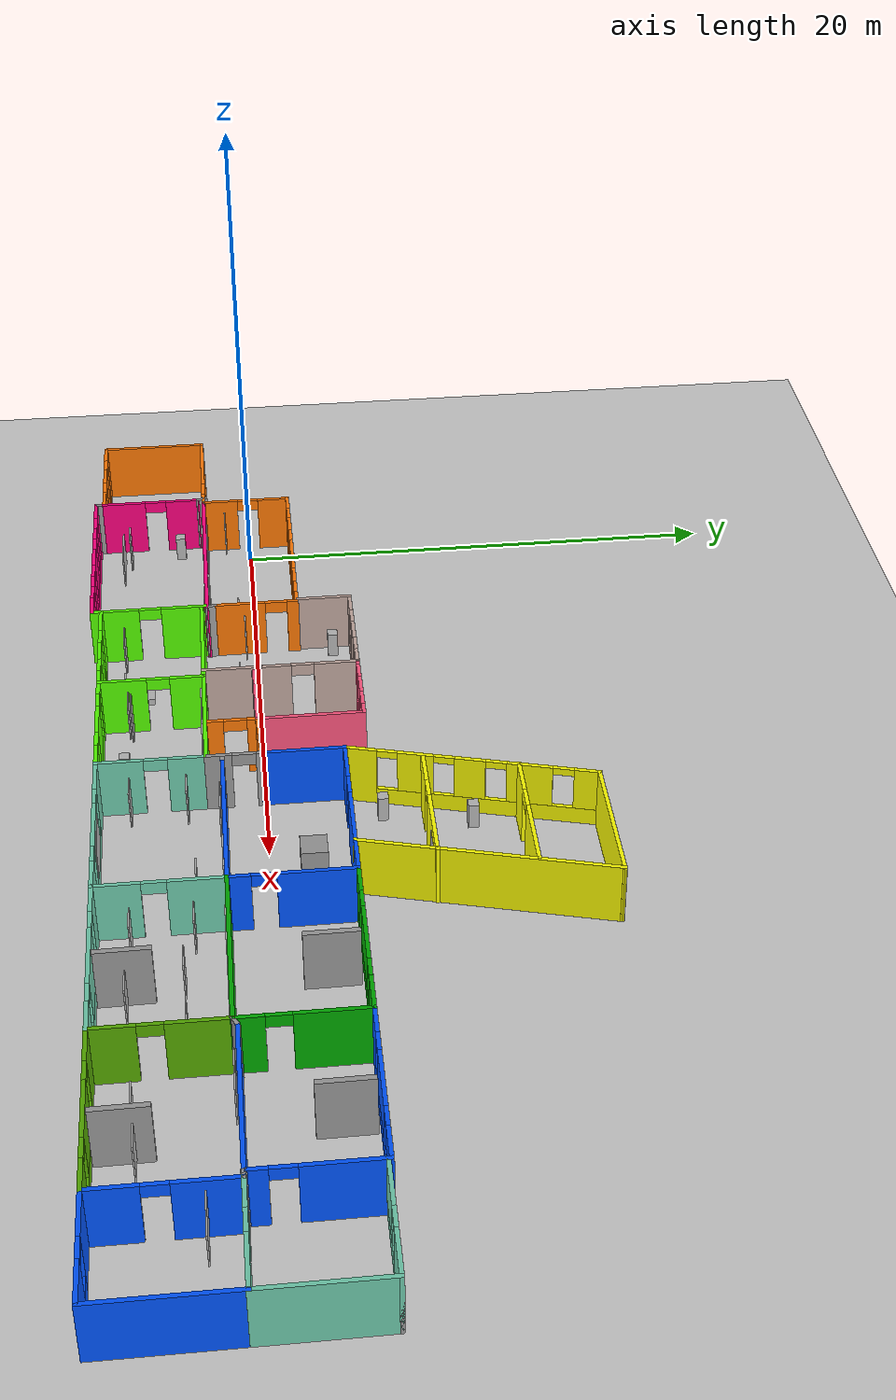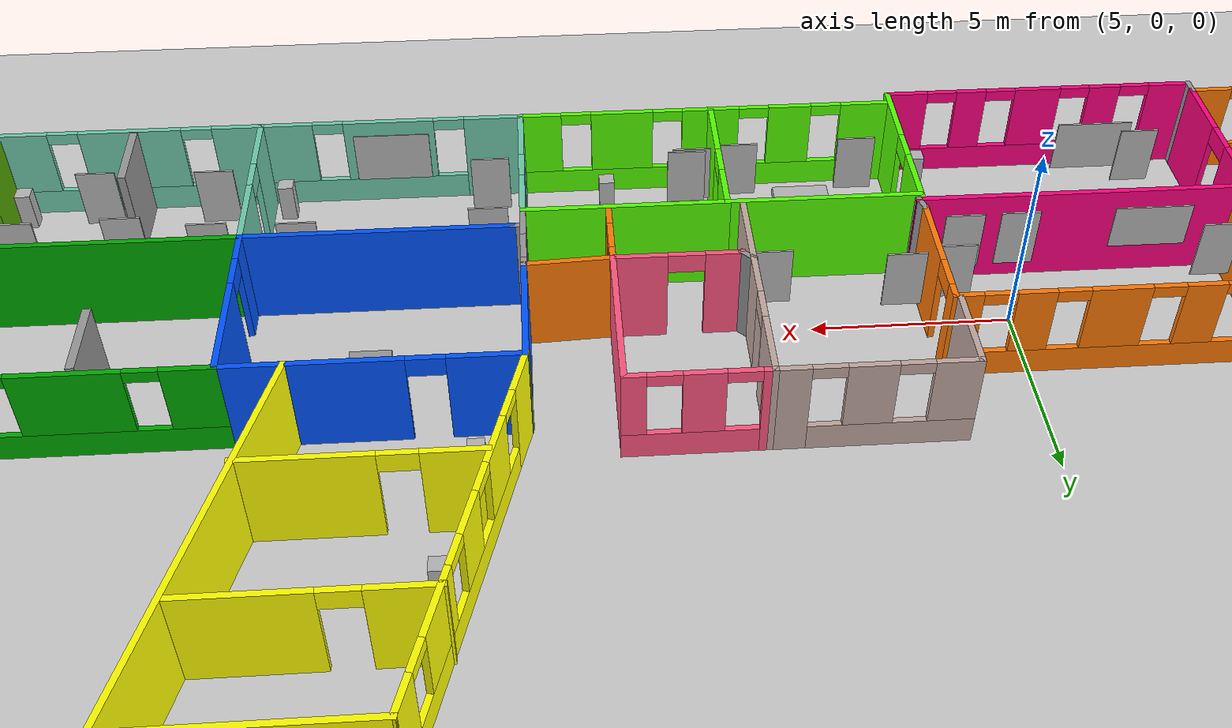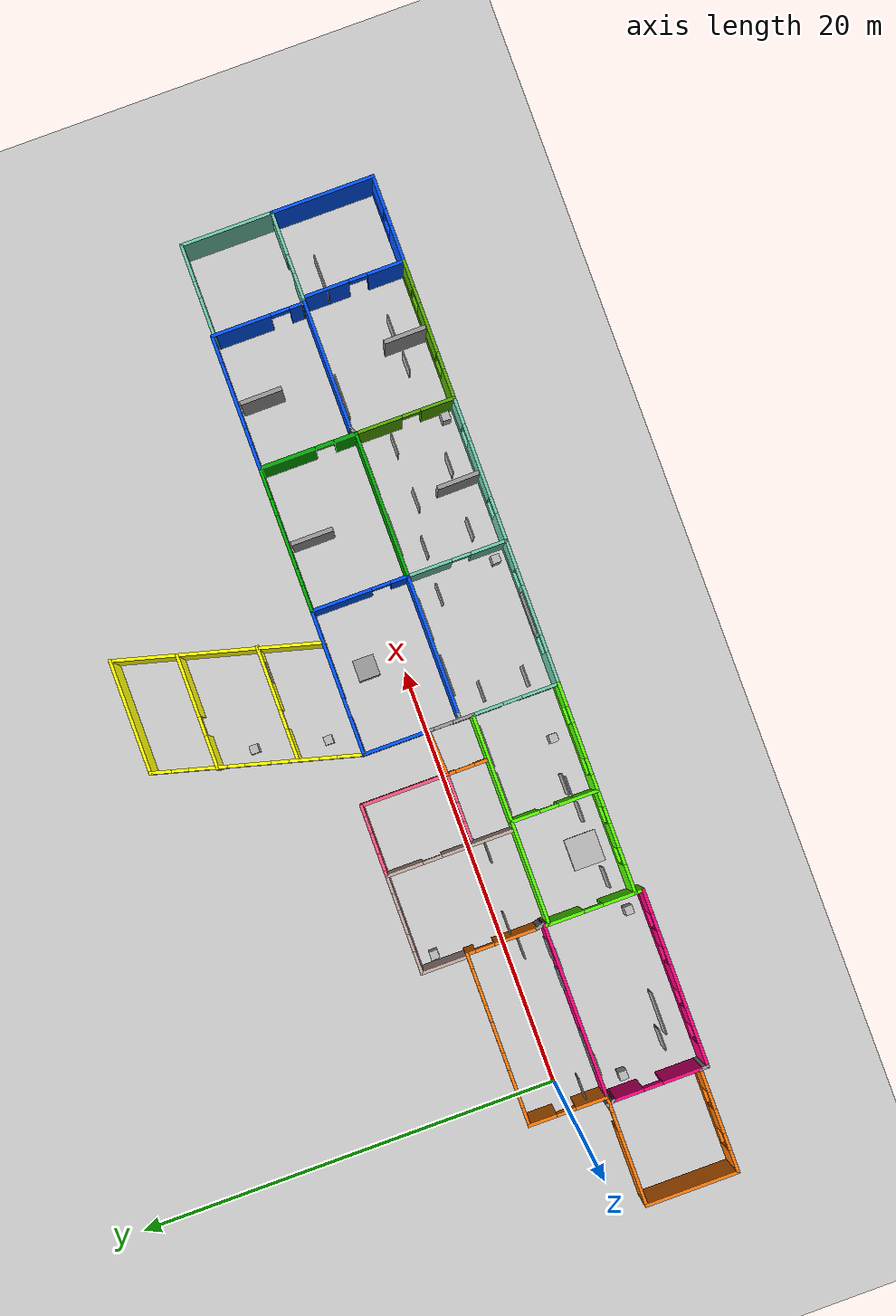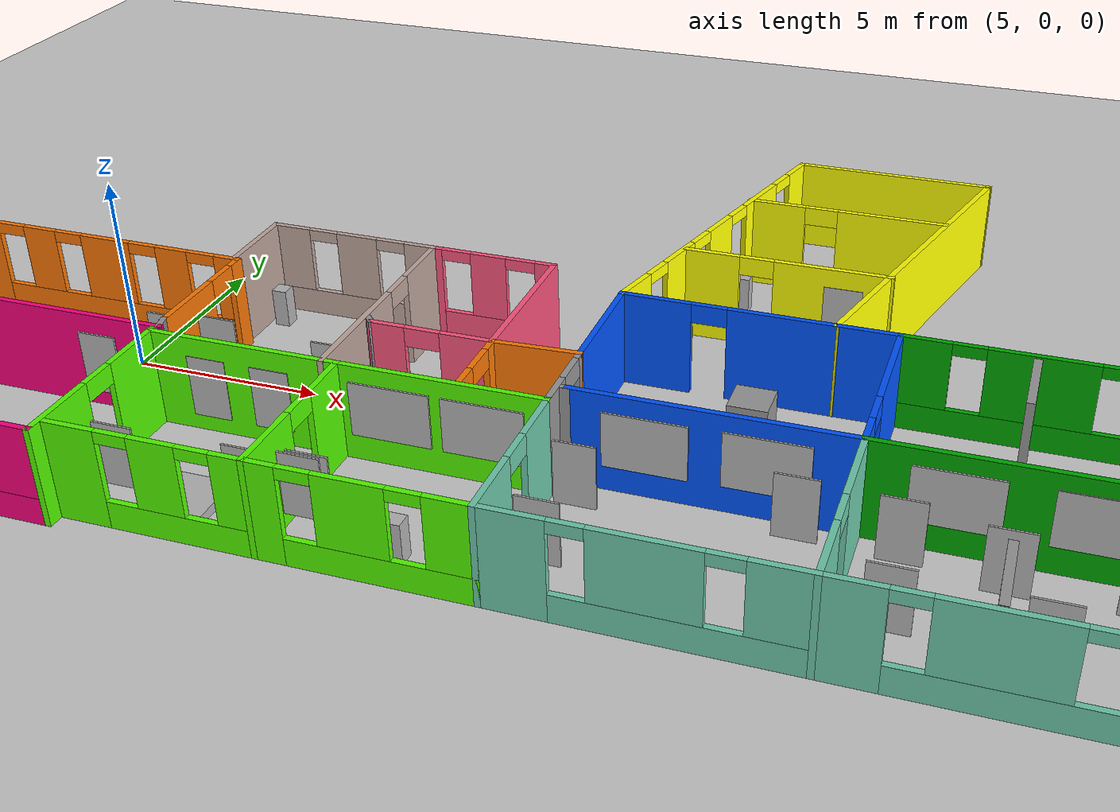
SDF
<sdf version="1.6">
 <world name="default">
  <light name="sun" type="directional">
   <pose>0 0 10 0 -0 0</pose>
   <diffuse>0.8 0.8 0.8 1</diffuse>
   <specular>0.2 0.2 0.2 1</specular>
   <attenuation>
    <range>1000</range>
    <constant>0.9</constant>
    <linear>0.01</linear>
    <quadratic>0.001</quadratic>
   </attenuation>
   <direction>-0.5 0.1 -0.9</direction>
  </light>
  <model name="ground_plane">
   <static>1</static>
   <link name="link">
    <collision name="collision">
     <geometry><plane><normal>0 0 1</normal><size>100 100</size></plane></geometry>
     <surface><friction><ode><mu>100</mu><mu2>50</mu2></ode></friction></surface>
    </collision>
    <visual name="visual">
     <cast_shadows>0</cast_shadows>
     <geometry><plane><normal>0 0 1</normal><size>100 100</size></plane></geometry>
     <material>
      <script><uri>file://media/materials/scripts/gazebo.material</uri><name>Gazebo/Grey</name></script>
     </material>
    </visual>
   </link>
  </model>
  <gravity>0 0 -9.8</gravity>
  <magnetic_field>6e-06 2.3e-05 -4.2e-05</magnetic_field>
  <atmosphere type="adiabatic"/>
  <physics name="default_physics" default="0" type="ode">
   <max_step_size>0.01</max_step_size>
   <real_time_factor>1</real_time_factor>
   <real_time_update_rate>100</real_time_update_rate>
  </physics>
  <scene><ambient>0.4 0.4 0.4 1</ambient><background>0.7 0.7 0.7 1</background><shadows>1</shadows></scene>
  <spherical_coordinates>
   <surface_model>EARTH_WGS84</surface_model>
   <latitude_deg>0</latitude_deg>
   <longitude_deg>0</longitude_deg>
   <elevation>0</elevation>
   <heading_deg>0</heading_deg>
  </spherical_coordinates>
  <model name="gallery2">
   <pose>17.6734 2.86394 0 0 -0 0</pose>
   <link name="Wall_0">
    <pose>-14.628 -1.09561 0 0 -0 0</pose>
    <visual name="Wall_0_Visual_0">
     <pose>-3.66723 0 1.25 0 -0 0</pose>
     <geometry><box><size>0.91554 0.15 2.5</size></box></geometry>
     <material>
      <script><uri>file://media/materials/scripts/gazebo.material</uri><name>Gazebo/Grey</name></script>
      <ambient>0.996078 0.47451 0.0196078 1</ambient>
     </material>
     <meta><layer>0</layer></meta>
    </visual>
    <collision name="Wall_0_Collision_0">
     <geometry><box><size>0.91554 0.15 2.5</size></box></geometry>
     <pose>-3.66723 0 1.25 0 -0 0</pose>
    </collision>
    <visual name="Wall_0_Visual_1">
     <pose>0.45777 0 0.35 0 -0 0</pose>
     <geometry><box><size>7.33446 0.15 0.7</size></box></geometry>
     <material>
      <script><uri>file://media/materials/scripts/gazebo.material</uri><name>Gazebo/Grey</name></script>
      <ambient>0.996078 0.47451 0.0196078 1</ambient>
     </material>
     <meta><layer>0</layer></meta>
    </visual>
    <collision name="Wall_0_Collision_1">
     <geometry><box><size>7.33446 0.15 0.7</size></box></geometry>
     <pose>0.45777 0 0.35 0 -0 0</pose>
    </collision>
    <visual name="Wall_0_Visual_2">
     <pose>-1.91944 0 1.6 0 -0 0</pose>
     <geometry><box><size>0.980046 0.15 1.8</size></box></geometry>
     <material>
      <script><uri>file://media/materials/scripts/gazebo.material</uri><name>Gazebo/Grey</name></script>
      <ambient>0.996078 0.47451 0.0196078 1</ambient>
     </material>
     <meta><layer>0</layer></meta>
    </visual>
    <collision name="Wall_0_Collision_2">
     <geometry><box><size>0.980046 0.15 1.8</size></box></geometry>
     <pose>-1.91944 0 1.6 0 -0 0</pose>
    </collision>
    <visual name="Wall_0_Visual_3">
     <pose>0.103342 0 1.6 0 -0 0</pose>
     <geometry><box><size>1.46551 0.15 1.8</size></box></geometry>
     <material>
      <script><uri>file://media/materials/scripts/gazebo.material</uri><name>Gazebo/Grey</name></script>
      <ambient>0.996078 0.47451 0.0196078 1</ambient>
     </material>
     <meta><layer>0</layer></meta>
    </visual>
    <collision name="Wall_0_Collision_3">
     <geometry><box><size>1.46551 0.15 1.8</size></box></geometry>
     <pose>0.103342 0 1.6 0 -0 0</pose>
    </collision>
    <visual name="Wall_0_Visual_4">
     <pose>2.10589 0 1.6 0 -0 0</pose>
     <geometry><box><size>0.93959 0.15 1.8</size></box></geometry>
     <material>
      <script><uri>file://media/materials/scripts/gazebo.material</uri><name>Gazebo/Grey</name></script>
      <ambient>0.996078 0.47451 0.0196078 1</ambient>
     </material>
     <meta><layer>0</layer></meta>
    </visual>
    <collision name="Wall_0_Collision_4">
     <geometry><box><size>0.93959 0.15 1.8</size></box></geometry>
     <pose>2.10589 0 1.6 0 -0 0</pose>
    </collision>
    <visual name="Wall_0_Visual_5">
     <pose>3.75034 0 1.6 0 -0 0</pose>
     <geometry><box><size>0.749312 0.15 1.8</size></box></geometry>
     <material>
      <script><uri>file://media/materials/scripts/gazebo.material</uri><name>Gazebo/Grey</name></script>
      <ambient>0.996078 0.47451 0.0196078 1</ambient>
     </material>
     <meta><layer>0</layer></meta>
    </visual>
    <collision name="Wall_0_Collision_5">
     <geometry><box><size>0.749312 0.15 1.8</size></box></geometry>
     <pose>3.75034 0 1.6 0 -0 0</pose>
    </collision>
    <visual name="Wall_0_Visual_6">
     <pose>-2.80946 0 2.35 0 -0 0</pose>
     <geometry><box><size>0.8 0.15 0.3</size></box></geometry>
     <material>
      <script><uri>file://media/materials/scripts/gazebo.material</uri><name>Gazebo/Grey</name></script>
      <ambient>0.996078 0.47451 0.0196078 1</ambient>
     </material>
     <meta><layer>0</layer></meta>
    </visual>
    <collision name="Wall_0_Collision_6">
     <geometry><box><size>0.8 0.15 0.3</size></box></geometry>
     <pose>-2.80946 0 2.35 0 -0 0</pose>
    </collision>
    <visual name="Wall_0_Visual_7">
     <pose>-1.02941 0 2.35 0 -0 0</pose>
     <geometry><box><size>0.8 0.15 0.3</size></box></geometry>
     <material>
      <script><uri>file://media/materials/scripts/gazebo.material</uri><name>Gazebo/Grey</name></script>
      <ambient>0.996078 0.47451 0.0196078 1</ambient>
     </material>
     <meta><layer>0</layer></meta>
    </visual>
    <collision name="Wall_0_Collision_7">
     <geometry><box><size>0.8 0.15 0.3</size></box></geometry>
     <pose>-1.02941 0 2.35 0 -0 0</pose>
    </collision>
    <visual name="Wall_0_Visual_8">
     <pose>1.2361 0 2.35 0 -0 0</pose>
     <geometry><box><size>0.8 0.15 0.3</size></box></geometry>
     <material>
      <script><uri>file://media/materials/scripts/gazebo.material</uri><name>Gazebo/Grey</name></script>
      <ambient>0.996078 0.47451 0.0196078 1</ambient>
     </material>
     <meta><layer>0</layer></meta>
    </visual>
    <collision name="Wall_0_Collision_8">
     <geometry><box><size>0.8 0.15 0.3</size></box></geometry>
     <pose>1.2361 0 2.35 0 -0 0</pose>
    </collision>
    <visual name="Wall_0_Visual_9">
     <pose>2.97569 0 2.35 0 -0 0</pose>
     <geometry><box><size>0.8 0.15 0.3</size></box></geometry>
     <material>
      <script><uri>file://media/materials/scripts/gazebo.material</uri><name>Gazebo/Grey</name></script>
      <ambient>0.996078 0.47451 0.0196078 1</ambient>
     </material>
     <meta><layer>0</layer></meta>
    </visual>
    <collision name="Wall_0_Collision_9">
     <geometry><box><size>0.8 0.15 0.3</size></box></geometry>
     <pose>2.97569 0 2.35 0 -0 0</pose>
    </collision>
   </link>
   <link name="Wall_1">
    <pose>-10.578 -2.77061 0 0 0 -1.5708</pose>
    <visual name="Wall_1_Visual_0">
     <pose>-1.51054 0 1.25 0 -0 0</pose>
     <geometry><box><size>0.478926 0.15 2.5</size></box></geometry>
     <material>
      <script><uri>file://media/materials/scripts/gazebo.material</uri><name>Gazebo/Grey</name></script>
      <ambient>0.996078 0.47451 0.0196078 1</ambient>
     </material>
     <meta><layer>0</layer></meta>
    </visual>
    <collision name="Wall_1_Collision_0">
     <geometry><box><size>0.478926 0.15 2.5</size></box></geometry>
     <pose>-1.51054 0 1.25 0 -0 0</pose>
    </collision>
    <visual name="Wall_1_Visual_1">
     <pose>0.689463 0 1.25 0 -0 0</pose>
     <geometry><box><size>2.12107 0.15 2.5</size></box></geometry>
     <material>
      <script><uri>file://media/materials/scripts/gazebo.material</uri><name>Gazebo/Grey</name></script>
      <ambient>0.996078 0.47451 0.0196078 1</ambient>
     </material>
     <meta><layer>0</layer></meta>
    </visual>
    <collision name="Wall_1_Collision_1">
     <geometry><box><size>2.12107 0.15 2.5</size></box></geometry>
     <pose>0.689463 0 1.25 0 -0 0</pose>
    </collision>
    <visual name="Wall_1_Visual_2">
     <pose>-0.821074 0 2.25 0 -0 0</pose>
     <geometry><box><size>0.9 0.15 0.5</size></box></geometry>
     <material>
      <script><uri>file://media/materials/scripts/gazebo.material</uri><name>Gazebo/Grey</name></script>
      <ambient>0.996078 0.47451 0.0196078 1</ambient>
     </material>
     <meta><layer>0</layer></meta>
    </visual>
    <collision name="Wall_1_Collision_2">
     <geometry><box><size>0.9 0.15 0.5</size></box></geometry>
     <pose>-0.821074 0 2.25 0 -0 0</pose>
    </collision>
   </link>
   <link name="Wall_10">
    <pose>-18.9374 -7.08368 0 0 -0 1.5708</pose>
    <visual name="Wall_10_Visual_0">
     <pose>-1.19077 0 1.25 0 -0 0</pose>
     <geometry><box><size>1.86845 0.15 2.5</size></box></geometry>
     <material>
      <script><uri>file://media/materials/scripts/gazebo.material</uri><name>Gazebo/Grey</name></script>
      <ambient>1 0 0.498039 1</ambient>
     </material>
     <meta><layer>0</layer></meta>
    </visual>
    <collision name="Wall_10_Collision_0">
     <geometry><box><size>1.86845 0.15 2.5</size></box></geometry>
     <pose>-1.19077 0 1.25 0 -0 0</pose>
    </collision>
    <visual name="Wall_10_Visual_1">
     <pose>1.38423 0 1.25 0 -0 0</pose>
     <geometry><box><size>1.48155 0.15 2.5</size></box></geometry>
     <material>
      <script><uri>file://media/materials/scripts/gazebo.material</uri><name>Gazebo/Grey</name></script>
      <ambient>1 0 0.498039 1</ambient>
     </material>
     <meta><layer>0</layer></meta>
    </visual>
    <collision name="Wall_10_Collision_1">
     <geometry><box><size>1.48155 0.15 2.5</size></box></geometry>
     <pose>1.38423 0 1.25 0 -0 0</pose>
    </collision>
    <visual name="Wall_10_Visual_2">
     <pose>0.193449 0 2.25 0 -0 0</pose>
     <geometry><box><size>0.9 0.15 0.5</size></box></geometry>
     <material>
      <script><uri>file://media/materials/scripts/gazebo.material</uri><name>Gazebo/Grey</name></script>
      <ambient>1 0 0.498039 1</ambient>
     </material>
     <meta><layer>0</layer></meta>
    </visual>
    <collision name="Wall_10_Collision_2">
     <geometry><box><size>0.9 0.15 0.5</size></box></geometry>
     <pose>0.193449 0 2.25 0 -0 0</pose>
    </collision>
   </link>
   <link name="Wall_12">
    <collision name="Wall_12_Collision">
     <geometry><box><size>0.5 0.15 2.5</size></box></geometry>
     <pose>0 0 1.25 0 -0 0</pose>
    </collision>
    <visual name="Wall_12_Visual">
     <pose>0 0 1.25 0 -0 0</pose>
     <geometry><box><size>0.5 0.15 2.5</size></box></geometry>
     <material>
      <script><uri>file://media/materials/scripts/gazebo.material</uri><name>Gazebo/Grey</name></script>
      <ambient>1 1 1 1</ambient>
     </material>
     <meta><layer>0</layer></meta>
    </visual>
    <pose>-18.9827 -4.86465 0 0 -0 1.8326</pose>
   </link>
   <link name="Wall_14">
    <collision name="Wall_14_Collision">
     <geometry><box><size>0.5 0.15 2.5</size></box></geometry>
     <pose>0 0 1.25 0 -0 0</pose>
    </collision>
    <visual name="Wall_14_Visual">
     <pose>0 0 1.25 0 -0 0</pose>
     <geometry><box><size>0.5 0.15 2.5</size></box></geometry>
     <material>
      <script><uri>file://media/materials/scripts/gazebo.material</uri><name>Gazebo/Grey</name></script>
      <ambient>1 1 1 1</ambient>
     </material>
     <meta><layer>0</layer></meta>
    </visual>
    <pose>-18.9374 -9.30869 0 0 0 -1.5708</pose>
   </link>
   <link name="Wall_15">
    <pose>-14.7624 -9.48368 0 0 -0 0</pose>
    <visual name="Wall_15_Visual_0">
     <pose>-3.6591 0 1.25 0 -0 0</pose>
     <geometry><box><size>1.18181 0.15 2.5</size></box></geometry>
     <material>
      <script><uri>file://media/materials/scripts/gazebo.material</uri><name>Gazebo/Grey</name></script>
      <ambient>1 0 0.498039 1</ambient>
     </material>
     <meta><layer>0</layer></meta>
    </visual>
    <collision name="Wall_15_Collision_0">
     <geometry><box><size>1.18181 0.15 2.5</size></box></geometry>
     <pose>-3.6591 0 1.25 0 -0 0</pose>
    </collision>
    <visual name="Wall_15_Visual_1">
     <pose>0.590905 0 0.35 0 -0 0</pose>
     <geometry><box><size>7.31819 0.15 0.7</size></box></geometry>
     <material>
      <script><uri>file://media/materials/scripts/gazebo.material</uri><name>Gazebo/Grey</name></script>
      <ambient>1 0 0.498039 1</ambient>
     </material>
     <meta><layer>0</layer></meta>
    </visual>
    <collision name="Wall_15_Collision_1">
     <geometry><box><size>7.31819 0.15 0.7</size></box></geometry>
     <pose>0.590905 0 0.35 0 -0 0</pose>
    </collision>
    <visual name="Wall_15_Visual_2">
     <pose>-1.83885 0 1.6 0 -0 0</pose>
     <geometry><box><size>0.858678 0.15 1.8</size></box></geometry>
     <material>
      <script><uri>file://media/materials/scripts/gazebo.material</uri><name>Gazebo/Grey</name></script>
      <ambient>1 0 0.498039 1</ambient>
     </material>
     <meta><layer>0</layer></meta>
    </visual>
    <collision name="Wall_15_Collision_2">
     <geometry><box><size>0.858678 0.15 1.8</size></box></geometry>
     <pose>-1.83885 0 1.6 0 -0 0</pose>
    </collision>
    <visual name="Wall_15_Visual_3">
     <pose>0.021909 0 1.6 0 -0 0</pose>
     <geometry><box><size>1.26284 0.15 1.8</size></box></geometry>
     <material>
      <script><uri>file://media/materials/scripts/gazebo.material</uri><name>Gazebo/Grey</name></script>
      <ambient>1 0 0.498039 1</ambient>
     </material>
     <meta><layer>0</layer></meta>
    </visual>
    <collision name="Wall_15_Collision_3">
     <geometry><box><size>1.26284 0.15 1.8</size></box></geometry>
     <pose>0.021909 0 1.6 0 -0 0</pose>
    </collision>
    <visual name="Wall_15_Visual_4">
     <pose>1.86264 0 1.6 0 -0 0</pose>
     <geometry><box><size>0.818617 0.15 1.8</size></box></geometry>
     <material>
      <script><uri>file://media/materials/scripts/gazebo.material</uri><name>Gazebo/Grey</name></script>
      <ambient>1 0 0.498039 1</ambient>
     </material>
     <meta><layer>0</layer></meta>
    </visual>
    <collision name="Wall_15_Collision_4">
     <geometry><box><size>0.818617 0.15 1.8</size></box></geometry>
     <pose>1.86264 0 1.6 0 -0 0</pose>
    </collision>
    <visual name="Wall_15_Visual_5">
     <pose>3.66097 0 1.6 0 -0 0</pose>
     <geometry><box><size>1.17805 0.15 1.8</size></box></geometry>
     <material>
      <script><uri>file://media/materials/scripts/gazebo.material</uri><name>Gazebo/Grey</name></script>
      <ambient>1 0 0.498039 1</ambient>
     </material>
     <meta><layer>0</layer></meta>
    </visual>
    <collision name="Wall_15_Collision_5">
     <geometry><box><size>1.17805 0.15 1.8</size></box></geometry>
     <pose>3.66097 0 1.6 0 -0 0</pose>
    </collision>
    <visual name="Wall_15_Visual_6">
     <pose>-2.66819 0 2.35 0 -0 0</pose>
     <geometry><box><size>0.8 0.15 0.3</size></box></geometry>
     <material>
      <script><uri>file://media/materials/scripts/gazebo.material</uri><name>Gazebo/Grey</name></script>
      <ambient>1 0 0.498039 1</ambient>
     </material>
     <meta><layer>0</layer></meta>
    </visual>
    <collision name="Wall_15_Collision_6">
     <geometry><box><size>0.8 0.15 0.3</size></box></geometry>
     <pose>-2.66819 0 2.35 0 -0 0</pose>
    </collision>
    <visual name="Wall_15_Visual_7">
     <pose>-1.00951 0 2.35 0 -0 0</pose>
     <geometry><box><size>0.8 0.15 0.3</size></box></geometry>
     <material>
      <script><uri>file://media/materials/scripts/gazebo.material</uri><name>Gazebo/Grey</name></script>
      <ambient>1 0 0.498039 1</ambient>
     </material>
     <meta><layer>0</layer></meta>
    </visual>
    <collision name="Wall_15_Collision_7">
     <geometry><box><size>0.8 0.15 0.3</size></box></geometry>
     <pose>-1.00951 0 2.35 0 -0 0</pose>
    </collision>
    <visual name="Wall_15_Visual_8">
     <pose>1.05333 0 2.35 0 -0 0</pose>
     <geometry><box><size>0.8 0.15 0.3</size></box></geometry>
     <material>
      <script><uri>file://media/materials/scripts/gazebo.material</uri><name>Gazebo/Grey</name></script>
      <ambient>1 0 0.498039 1</ambient>
     </material>
     <meta><layer>0</layer></meta>
    </visual>
    <collision name="Wall_15_Collision_8">
     <geometry><box><size>0.8 0.15 0.3</size></box></geometry>
     <pose>1.05333 0 2.35 0 -0 0</pose>
    </collision>
    <visual name="Wall_15_Visual_9">
     <pose>2.67195 0 2.35 0 -0 0</pose>
     <geometry><box><size>0.8 0.15 0.3</size></box></geometry>
     <material>
      <script><uri>file://media/materials/scripts/gazebo.material</uri><name>Gazebo/Grey</name></script>
      <ambient>1 0 0.498039 1</ambient>
     </material>
     <meta><layer>0</layer></meta>
    </visual>
    <collision name="Wall_15_Collision_9">
     <geometry><box><size>0.8 0.15 0.3</size></box></geometry>
     <pose>2.67195 0 2.35 0 -0 0</pose>
    </collision>
   </link>
   <link name="Wall_16">
    <pose>-10.5874 -7.18368 0 0 -0 1.5708</pose>
    <visual name="Wall_16_Visual_0">
     <pose>-1.37565 0 1.25 0 -0 0</pose>
     <geometry><box><size>1.99871 0.15 2.5</size></box></geometry>
     <material>
      <script><uri>file://media/materials/scripts/gazebo.material</uri><name>Gazebo/Grey</name></script>
      <ambient>0.333333 1 0 1</ambient>
     </material>
     <meta><layer>0</layer></meta>
    </visual>
    <collision name="Wall_16_Collision_0">
     <geometry><box><size>1.99871 0.15 2.5</size></box></geometry>
     <pose>-1.37565 0 1.25 0 -0 0</pose>
    </collision>
    <visual name="Wall_16_Visual_1">
     <pose>1.44935 0 1.25 0 -0 0</pose>
     <geometry><box><size>1.85129 0.15 2.5</size></box></geometry>
     <material>
      <script><uri>file://media/materials/scripts/gazebo.material</uri><name>Gazebo/Grey</name></script>
      <ambient>0.333333 1 0 1</ambient>
     </material>
     <meta><layer>0</layer></meta>
    </visual>
    <collision name="Wall_16_Collision_1">
     <geometry><box><size>1.85129 0.15 2.5</size></box></geometry>
     <pose>1.44935 0 1.25 0 -0 0</pose>
    </collision>
    <visual name="Wall_16_Visual_2">
     <pose>0.073709 0 2.25 0 -0 0</pose>
     <geometry><box><size>0.9 0.15 0.5</size></box></geometry>
     <material>
      <script><uri>file://media/materials/scripts/gazebo.material</uri><name>Gazebo/Grey</name></script>
      <ambient>0.333333 1 0 1</ambient>
     </material>
     <meta><layer>0</layer></meta>
    </visual>
    <collision name="Wall_16_Collision_2">
     <geometry><box><size>0.9 0.15 0.5</size></box></geometry>
     <pose>0.073709 0 2.25 0 -0 0</pose>
    </collision>
   </link>
   <link name="Wall_19">
    <pose>-8.1376 -9.10606 0 0 -0 0</pose>
    <visual name="Wall_19_Visual_0">
     <pose>-1.79893 0 1.25 0 -0 0</pose>
     <geometry><box><size>1.40214 0.15 2.5</size></box></geometry>
     <material>
      <script><uri>file://media/materials/scripts/gazebo.material</uri><name>Gazebo/Grey</name></script>
      <ambient>0.333333 1 0 1</ambient>
     </material>
     <meta><layer>0</layer></meta>
    </visual>
    <collision name="Wall_19_Collision_0">
     <geometry><box><size>1.40214 0.15 2.5</size></box></geometry>
     <pose>-1.79893 0 1.25 0 -0 0</pose>
    </collision>
    <visual name="Wall_19_Visual_1">
     <pose>0.701072 0 0.35 0 -0 0</pose>
     <geometry><box><size>3.59786 0.15 0.7</size></box></geometry>
     <material>
      <script><uri>file://media/materials/scripts/gazebo.material</uri><name>Gazebo/Grey</name></script>
      <ambient>0.333333 1 0 1</ambient>
     </material>
     <meta><layer>0</layer></meta>
    </visual>
    <collision name="Wall_19_Collision_1">
     <geometry><box><size>3.59786 0.15 0.7</size></box></geometry>
     <pose>0.701072 0 0.35 0 -0 0</pose>
    </collision>
    <visual name="Wall_19_Visual_2">
     <pose>0.279145 0 1.6 0 -0 0</pose>
     <geometry><box><size>1.154 0.15 1.8</size></box></geometry>
     <material>
      <script><uri>file://media/materials/scripts/gazebo.material</uri><name>Gazebo/Grey</name></script>
      <ambient>0.333333 1 0 1</ambient>
     </material>
     <meta><layer>0</layer></meta>
    </visual>
    <collision name="Wall_19_Collision_2">
     <geometry><box><size>1.154 0.15 1.8</size></box></geometry>
     <pose>0.279145 0 1.6 0 -0 0</pose>
    </collision>
    <visual name="Wall_19_Visual_3">
     <pose>2.07807 0 1.6 0 -0 0</pose>
     <geometry><box><size>0.843853 0.15 1.8</size></box></geometry>
     <material>
      <script><uri>file://media/materials/scripts/gazebo.material</uri><name>Gazebo/Grey</name></script>
      <ambient>0.333333 1 0 1</ambient>
     </material>
     <meta><layer>0</layer></meta>
    </visual>
    <collision name="Wall_19_Collision_3">
     <geometry><box><size>0.843853 0.15 1.8</size></box></geometry>
     <pose>2.07807 0 1.6 0 -0 0</pose>
    </collision>
    <visual name="Wall_19_Visual_4">
     <pose>-0.697857 0 2.35 0 -0 0</pose>
     <geometry><box><size>0.8 0.15 0.3</size></box></geometry>
     <material>
      <script><uri>file://media/materials/scripts/gazebo.material</uri><name>Gazebo/Grey</name></script>
      <ambient>0.333333 1 0 1</ambient>
     </material>
     <meta><layer>0</layer></meta>
    </visual>
    <collision name="Wall_19_Collision_4">
     <geometry><box><size>0.8 0.15 0.3</size></box></geometry>
     <pose>-0.697857 0 2.35 0 -0 0</pose>
    </collision>
    <visual name="Wall_19_Visual_5">
     <pose>1.25615 0 2.35 0 -0 0</pose>
     <geometry><box><size>0.8 0.15 0.3</size></box></geometry>
     <material>
      <script><uri>file://media/materials/scripts/gazebo.material</uri><name>Gazebo/Grey</name></script>
      <ambient>0.333333 1 0 1</ambient>
     </material>
     <meta><layer>0</layer></meta>
    </visual>
    <collision name="Wall_19_Collision_5">
     <geometry><box><size>0.8 0.15 0.3</size></box></geometry>
     <pose>1.25615 0 2.35 0 -0 0</pose>
    </collision>
   </link>
   <link name="Wall_2">
    <collision name="Wall_2_Collision">
     <geometry><box><size>0.5 0.15 2.5</size></box></geometry>
     <pose>0 0 1.25 0 -0 0</pose>
    </collision>
    <visual name="Wall_2_Visual">
     <pose>0 0 1.25 0 -0 0</pose>
     <geometry><box><size>0.5 0.15 2.5</size></box></geometry>
     <material>
      <script><uri>file://media/materials/scripts/gazebo.material</uri><name>Gazebo/Grey</name></script>
      <ambient>1 1 1 1</ambient>
     </material>
     <meta><layer>0</layer></meta>
    </visual>
    <pose>-10.5327 -4.61465 0 0 0 -1.309</pose>
   </link>
   <link name="Wall_20">
    <pose>-5.7126 -7.05606 0 0 -0 1.5708</pose>
    <visual name="Wall_20_Visual_0">
     <pose>-1.15486 0 1.25 0 -0 0</pose>
     <geometry><box><size>1.94029 0.15 2.5</size></box></geometry>
     <material>
      <script><uri>file://media/materials/scripts/gazebo.material</uri><name>Gazebo/Grey</name></script>
      <ambient>0.333333 1 0 1</ambient>
     </material>
     <meta><layer>0</layer></meta>
    </visual>
    <collision name="Wall_20_Collision_0">
     <geometry><box><size>1.94029 0.15 2.5</size></box></geometry>
     <pose>-1.15486 0 1.25 0 -0 0</pose>
    </collision>
    <visual name="Wall_20_Visual_1">
     <pose>1.42014 0 1.25 0 -0 0</pose>
     <geometry><box><size>1.40971 0.15 2.5</size></box></geometry>
     <material>
      <script><uri>file://media/materials/scripts/gazebo.material</uri><name>Gazebo/Grey</name></script>
      <ambient>0.333333 1 0 1</ambient>
     </material>
     <meta><layer>0</layer></meta>
    </visual>
    <collision name="Wall_20_Collision_1">
     <geometry><box><size>1.40971 0.15 2.5</size></box></geometry>
     <pose>1.42014 0 1.25 0 -0 0</pose>
    </collision>
    <visual name="Wall_20_Visual_2">
     <pose>0.265286 0 2.25 0 -0 0</pose>
     <geometry><box><size>0.9 0.15 0.5</size></box></geometry>
     <material>
      <script><uri>file://media/materials/scripts/gazebo.material</uri><name>Gazebo/Grey</name></script>
      <ambient>0.333333 1 0 1</ambient>
     </material>
     <meta><layer>0</layer></meta>
    </visual>
    <collision name="Wall_20_Collision_2">
     <geometry><box><size>0.9 0.15 0.5</size></box></geometry>
     <pose>0.265286 0 2.25 0 -0 0</pose>
    </collision>
   </link>
   <link name="Wall_21">
    <collision name="Wall_21_Collision">
     <geometry><box><size>5 0.15 2.5</size></box></geometry>
     <pose>0 0 1.25 0 -0 0</pose>
    </collision>
    <visual name="Wall_21_Visual">
     <pose>0 0 1.25 0 -0 0</pose>
     <geometry><box><size>5 0.15 2.5</size></box></geometry>
     <material>
      <script><uri>file://media/materials/scripts/gazebo.material</uri><name>Gazebo/Grey</name></script>
      <ambient>0.333333 1 0 1</ambient>
     </material>
     <meta><layer>0</layer></meta>
    </visual>
    <pose>-8.1376 -5.00606 0 0 -0 3.14159</pose>
   </link>
   <link name="Wall_23">
    <pose>-6.08514 -1.96338 0 0 -0 1.5708</pose>
    <visual name="Wall_23_Visual_0">
     <pose>-1.35497 0 1.25 0 -0 0</pose>
     <geometry><box><size>3.54005 0.15 2.5</size></box></geometry>
     <material>
      <script><uri>file://media/materials/scripts/gazebo.material</uri><name>Gazebo/Grey</name></script>
      <ambient>0.760784 0.662745 0.627451 1</ambient>
     </material>
     <meta><layer>0</layer></meta>
    </visual>
    <collision name="Wall_23_Collision_0">
     <geometry><box><size>3.54005 0.15 2.5</size></box></geometry>
     <pose>-1.35497 0 1.25 0 -0 0</pose>
    </collision>
    <visual name="Wall_23_Visual_1">
     <pose>2.22003 0 1.25 0 -0 0</pose>
     <geometry><box><size>1.80995 0.15 2.5</size></box></geometry>
     <material>
      <script><uri>file://media/materials/scripts/gazebo.material</uri><name>Gazebo/Grey</name></script>
      <ambient>0.760784 0.662745 0.627451 1</ambient>
     </material>
     <meta><layer>0</layer></meta>
    </visual>
    <collision name="Wall_23_Collision_1">
     <geometry><box><size>1.80995 0.15 2.5</size></box></geometry>
     <pose>2.22003 0 1.25 0 -0 0</pose>
    </collision>
    <visual name="Wall_23_Visual_2">
     <pose>0.865054 0 2.25 0 -0 0</pose>
     <geometry><box><size>0.9 0.15 0.5</size></box></geometry>
     <material>
      <script><uri>file://media/materials/scripts/gazebo.material</uri><name>Gazebo/Grey</name></script>
      <ambient>0.760784 0.662745 0.627451 1</ambient>
     </material>
     <meta><layer>0</layer></meta>
    </visual>
    <collision name="Wall_23_Collision_2">
     <geometry><box><size>0.9 0.15 0.5</size></box></geometry>
     <pose>0.865054 0 2.25 0 -0 0</pose>
    </collision>
   </link>
   <link name="Wall_24">
    <pose>-8.38514 1.08662 0 0 -0 3.14159</pose>
    <visual name="Wall_24_Visual_0">
     <pose>-1.92999 0 1.25 0 -0 0</pose>
     <geometry><box><size>0.890024 0.15 2.5</size></box></geometry>
     <material>
      <script><uri>file://media/materials/scripts/gazebo.material</uri><name>Gazebo/Grey</name></script>
      <ambient>0.760784 0.662745 0.627451 1</ambient>
     </material>
     <meta><layer>0</layer></meta>
    </visual>
    <collision name="Wall_24_Collision_0">
     <geometry><box><size>0.890024 0.15 2.5</size></box></geometry>
     <pose>-1.92999 0 1.25 0 -0 0</pose>
    </collision>
    <visual name="Wall_24_Visual_1">
     <pose>0.445012 0 0.35 0 -0 0</pose>
     <geometry><box><size>3.85998 0.15 0.7</size></box></geometry>
     <material>
      <script><uri>file://media/materials/scripts/gazebo.material</uri><name>Gazebo/Grey</name></script>
      <ambient>0.760784 0.662745 0.627451 1</ambient>
     </material>
     <meta><layer>0</layer></meta>
    </visual>
    <collision name="Wall_24_Collision_1">
     <geometry><box><size>3.85998 0.15 0.7</size></box></geometry>
     <pose>0.445012 0 0.35 0 -0 0</pose>
    </collision>
    <visual name="Wall_24_Visual_2">
     <pose>-0.107974 0 1.6 0 -0 0</pose>
     <geometry><box><size>1.154 0.15 1.8</size></box></geometry>
     <material>
      <script><uri>file://media/materials/scripts/gazebo.material</uri><name>Gazebo/Grey</name></script>
      <ambient>0.760784 0.662745 0.627451 1</ambient>
     </material>
     <meta><layer>0</layer></meta>
    </visual>
    <collision name="Wall_24_Collision_2">
     <geometry><box><size>1.154 0.15 1.8</size></box></geometry>
     <pose>-0.107974 0 1.6 0 -0 0</pose>
    </collision>
    <visual name="Wall_24_Visual_3">
     <pose>1.82201 0 1.6 0 -0 0</pose>
     <geometry><box><size>1.10597 0.15 1.8</size></box></geometry>
     <material>
      <script><uri>file://media/materials/scripts/gazebo.material</uri><name>Gazebo/Grey</name></script>
      <ambient>0.760784 0.662745 0.627451 1</ambient>
     </material>
     <meta><layer>0</layer></meta>
    </visual>
    <collision name="Wall_24_Collision_3">
     <geometry><box><size>1.10597 0.15 1.8</size></box></geometry>
     <pose>1.82201 0 1.6 0 -0 0</pose>
    </collision>
    <visual name="Wall_24_Visual_4">
     <pose>-1.08498 0 2.35 0 -0 0</pose>
     <geometry><box><size>0.8 0.15 0.3</size></box></geometry>
     <material>
      <script><uri>file://media/materials/scripts/gazebo.material</uri><name>Gazebo/Grey</name></script>
      <ambient>0.760784 0.662745 0.627451 1</ambient>
     </material>
     <meta><layer>0</layer></meta>
    </visual>
    <collision name="Wall_24_Collision_4">
     <geometry><box><size>0.8 0.15 0.3</size></box></geometry>
     <pose>-1.08498 0 2.35 0 -0 0</pose>
    </collision>
    <visual name="Wall_24_Visual_5">
     <pose>0.869028 0 2.35 0 -0 0</pose>
     <geometry><box><size>0.8 0.15 0.3</size></box></geometry>
     <material>
      <script><uri>file://media/materials/scripts/gazebo.material</uri><name>Gazebo/Grey</name></script>
      <ambient>0.760784 0.662745 0.627451 1</ambient>
     </material>
     <meta><layer>0</layer></meta>
    </visual>
    <collision name="Wall_24_Collision_5">
     <geometry><box><size>0.8 0.15 0.3</size></box></geometry>
     <pose>0.869028 0 2.35 0 -0 0</pose>
    </collision>
   </link>
   <link name="Wall_25">
    <collision name="Wall_25_Collision">
     <geometry><box><size>2.25 0.15 2.5</size></box></geometry>
     <pose>0 0 1.25 0 -0 0</pose>
    </collision>
    <visual name="Wall_25_Visual">
     <pose>0 0 1.25 0 -0 0</pose>
     <geometry><box><size>2.25 0.15 2.5</size></box></geometry>
     <material>
      <script><uri>file://media/materials/scripts/gazebo.material</uri><name>Gazebo/Grey</name></script>
      <ambient>0.760784 0.662745 0.627451 1</ambient>
     </material>
     <meta><layer>0</layer></meta>
    </visual>
    <pose>-10.6851 0.036615 0 0 0 -1.5708</pose>
   </link>
   <link name="Wall_27">
    <pose>-4.41014 1.08662 0 0 -0 0</pose>
    <visual name="Wall_27_Visual_0">
     <pose>-1.58096 0 1.25 0 -0 0</pose>
     <geometry><box><size>0.338071 0.15 2.5</size></box></geometry>
     <material>
      <script><uri>file://media/materials/scripts/gazebo.material</uri><name>Gazebo/Grey</name></script>
      <ambient>1 0.333333 0.498039 1</ambient>
     </material>
     <meta><layer>0</layer></meta>
    </visual>
    <collision name="Wall_27_Collision_0">
     <geometry><box><size>0.338071 0.15 2.5</size></box></geometry>
     <pose>-1.58096 0 1.25 0 -0 0</pose>
    </collision>
    <visual name="Wall_27_Visual_1">
     <pose>0.169036 0 0.35 0 -0 0</pose>
     <geometry><box><size>3.16193 0.15 0.7</size></box></geometry>
     <material>
      <script><uri>file://media/materials/scripts/gazebo.material</uri><name>Gazebo/Grey</name></script>
      <ambient>1 0.333333 0.498039 1</ambient>
     </material>
     <meta><layer>0</layer></meta>
    </visual>
    <collision name="Wall_27_Collision_1">
     <geometry><box><size>3.16193 0.15 0.7</size></box></geometry>
     <pose>0.169036 0 0.35 0 -0 0</pose>
    </collision>
    <visual name="Wall_27_Visual_2">
     <pose>-0.12194 0 1.6 0 -0 0</pose>
     <geometry><box><size>0.979976 0.15 1.8</size></box></geometry>
     <material>
      <script><uri>file://media/materials/scripts/gazebo.material</uri><name>Gazebo/Grey</name></script>
      <ambient>1 0.333333 0.498039 1</ambient>
     </material>
     <meta><layer>0</layer></meta>
    </visual>
    <collision name="Wall_27_Collision_2">
     <geometry><box><size>0.979976 0.15 1.8</size></box></geometry>
     <pose>-0.12194 0 1.6 0 -0 0</pose>
    </collision>
    <visual name="Wall_27_Visual_3">
     <pose>1.45902 0 1.6 0 -0 0</pose>
     <geometry><box><size>0.581952 0.15 1.8</size></box></geometry>
     <material>
      <script><uri>file://media/materials/scripts/gazebo.material</uri><name>Gazebo/Grey</name></script>
      <ambient>1 0.333333 0.498039 1</ambient>
     </material>
     <meta><layer>0</layer></meta>
    </visual>
    <collision name="Wall_27_Collision_3">
     <geometry><box><size>0.581952 0.15 1.8</size></box></geometry>
     <pose>1.45902 0 1.6 0 -0 0</pose>
    </collision>
    <visual name="Wall_27_Visual_4">
     <pose>-1.01193 0 2.35 0 -0 0</pose>
     <geometry><box><size>0.8 0.15 0.3</size></box></geometry>
     <material>
      <script><uri>file://media/materials/scripts/gazebo.material</uri><name>Gazebo/Grey</name></script>
      <ambient>1 0.333333 0.498039 1</ambient>
     </material>
     <meta><layer>0</layer></meta>
    </visual>
    <collision name="Wall_27_Collision_4">
     <geometry><box><size>0.8 0.15 0.3</size></box></geometry>
     <pose>-1.01193 0 2.35 0 -0 0</pose>
    </collision>
    <visual name="Wall_27_Visual_5">
     <pose>0.768048 0 2.35 0 -0 0</pose>
     <geometry><box><size>0.8 0.15 0.3</size></box></geometry>
     <material>
      <script><uri>file://media/materials/scripts/gazebo.material</uri><name>Gazebo/Grey</name></script>
      <ambient>1 0.333333 0.498039 1</ambient>
     </material>
     <meta><layer>0</layer></meta>
    </visual>
    <collision name="Wall_27_Collision_5">
     <geometry><box><size>0.8 0.15 0.3</size></box></geometry>
     <pose>0.768048 0 2.35 0 -0 0</pose>
    </collision>
   </link>
   <link name="Wall_28">
    <collision name="Wall_28_Collision">
     <geometry><box><size>4.25 0.15 2.5</size></box></geometry>
     <pose>0 0 1.25 0 -0 0</pose>
    </collision>
    <visual name="Wall_28_Visual">
     <pose>0 0 1.25 0 -0 0</pose>
     <geometry><box><size>4.25 0.15 2.5</size></box></geometry>
     <material>
      <script><uri>file://media/materials/scripts/gazebo.material</uri><name>Gazebo/Grey</name></script>
      <ambient>1 0.333333 0.498039 1</ambient>
     </material>
     <meta><layer>0</layer></meta>
    </visual>
    <pose>-2.73514 -0.963385 0 0 0 -1.5708</pose>
   </link>
   <link name="Wall_29">
    <pose>-4.28514 -3.01338 0 0 -0 3.14159</pose>
    <visual name="Wall_29_Visual_0">
     <pose>-0.928845 0 1.25 0 -0 0</pose>
     <geometry><box><size>1.39231 0.15 2.5</size></box></geometry>
     <material>
      <script><uri>file://media/materials/scripts/gazebo.material</uri><name>Gazebo/Grey</name></script>
      <ambient>1 0.333333 0.498039 1</ambient>
     </material>
     <meta><layer>0</layer></meta>
    </visual>
    <collision name="Wall_29_Collision_0">
     <geometry><box><size>1.39231 0.15 2.5</size></box></geometry>
     <pose>-0.928845 0 1.25 0 -0 0</pose>
    </collision>
    <visual name="Wall_29_Visual_1">
     <pose>1.14616 0 1.25 0 -0 0</pose>
     <geometry><box><size>0.95769 0.15 2.5</size></box></geometry>
     <material>
      <script><uri>file://media/materials/scripts/gazebo.material</uri><name>Gazebo/Grey</name></script>
      <ambient>1 0.333333 0.498039 1</ambient>
     </material>
     <meta><layer>0</layer></meta>
    </visual>
    <collision name="Wall_29_Collision_1">
     <geometry><box><size>0.95769 0.15 2.5</size></box></geometry>
     <pose>1.14616 0 1.25 0 -0 0</pose>
    </collision>
    <visual name="Wall_29_Visual_2">
     <pose>0.21731 0 2.25 0 -0 0</pose>
     <geometry><box><size>0.9 0.15 0.5</size></box></geometry>
     <material>
      <script><uri>file://media/materials/scripts/gazebo.material</uri><name>Gazebo/Grey</name></script>
      <ambient>1 0.333333 0.498039 1</ambient>
     </material>
     <meta><layer>0</layer></meta>
    </visual>
    <collision name="Wall_29_Collision_2">
     <geometry><box><size>0.9 0.15 0.5</size></box></geometry>
     <pose>0.21731 0 2.25 0 -0 0</pose>
    </collision>
   </link>
   <link name="Wall_3">
    <collision name="Wall_3_Collision">
     <geometry><box><size>8.25 0.15 2.5</size></box></geometry>
     <pose>0 0 1.25 0 -0 0</pose>
    </collision>
    <visual name="Wall_3_Visual">
     <pose>0 0 1.25 0 -0 0</pose>
     <geometry><box><size>8.25 0.15 2.5</size></box></geometry>
     <material>
      <script><uri>file://media/materials/scripts/gazebo.material</uri><name>Gazebo/Grey</name></script>
      <ambient>1 0 0.498039 1</ambient>
     </material>
     <meta><layer>0</layer></meta>
    </visual>
    <pose>-14.5374 -4.78369 0 0 -0 3.14159</pose>
   </link>
   <link name="Wall_31">
    <collision name="Wall_31_Collision">
     <geometry><box><size>0.5 0.15 2.5</size></box></geometry>
     <pose>0 0 1.25 0 -0 0</pose>
    </collision>
    <visual name="Wall_31_Visual">
     <pose>0 0 1.25 0 -0 0</pose>
     <geometry><box><size>0.5 0.15 2.5</size></box></geometry>
     <material>
      <script><uri>file://media/materials/scripts/gazebo.material</uri><name>Gazebo/Grey</name></script>
      <ambient>1 1 1 1</ambient>
     </material>
     <meta><layer>0</layer></meta>
    </visual>
    <pose>-5.95889 -2.88964 0 0 -0 2.35619</pose>
   </link>
   <link name="Wall_33">
    <pose>-3.1626 -9.10606 0 0 -0 0</pose>
    <visual name="Wall_33_Visual_0">
     <pose>-2.20883 0 1.25 0 -0 0</pose>
     <geometry><box><size>0.832343 0.15 2.5</size></box></geometry>
     <material>
      <script><uri>file://media/materials/scripts/gazebo.material</uri><name>Gazebo/Grey</name></script>
      <ambient>0.333333 1 0 1</ambient>
     </material>
     <meta><layer>0</layer></meta>
    </visual>
    <collision name="Wall_33_Collision_0">
     <geometry><box><size>0.832343 0.15 2.5</size></box></geometry>
     <pose>-2.20883 0 1.25 0 -0 0</pose>
    </collision>
    <visual name="Wall_33_Visual_1">
     <pose>0.416172 0 0.35 0 -0 0</pose>
     <geometry><box><size>4.41766 0.15 0.7</size></box></geometry>
     <material>
      <script><uri>file://media/materials/scripts/gazebo.material</uri><name>Gazebo/Grey</name></script>
      <ambient>0.333333 1 0 1</ambient>
     </material>
     <meta><layer>0</layer></meta>
    </visual>
    <collision name="Wall_33_Collision_1">
     <geometry><box><size>4.41766 0.15 0.7</size></box></geometry>
     <pose>0.416172 0 0.35 0 -0 0</pose>
    </collision>
    <visual name="Wall_33_Visual_2">
     <pose>-0.163992 0 1.6 0 -0 0</pose>
     <geometry><box><size>1.65733 0.15 1.8</size></box></geometry>
     <material>
      <script><uri>file://media/materials/scripts/gazebo.material</uri><name>Gazebo/Grey</name></script>
      <ambient>0.333333 1 0 1</ambient>
     </material>
     <meta><layer>0</layer></meta>
    </visual>
    <collision name="Wall_33_Collision_2">
     <geometry><box><size>1.65733 0.15 1.8</size></box></geometry>
     <pose>-0.163992 0 1.6 0 -0 0</pose>
    </collision>
    <visual name="Wall_33_Visual_3">
     <pose>2.04484 0 1.6 0 -0 0</pose>
     <geometry><box><size>1.16033 0.15 1.8</size></box></geometry>
     <material>
      <script><uri>file://media/materials/scripts/gazebo.material</uri><name>Gazebo/Grey</name></script>
      <ambient>0.333333 1 0 1</ambient>
     </material>
     <meta><layer>0</layer></meta>
    </visual>
    <collision name="Wall_33_Collision_3">
     <geometry><box><size>1.16033 0.15 1.8</size></box></geometry>
     <pose>2.04484 0 1.6 0 -0 0</pose>
    </collision>
    <visual name="Wall_33_Visual_4">
     <pose>-1.39266 0 2.35 0 -0 0</pose>
     <geometry><box><size>0.8 0.15 0.3</size></box></geometry>
     <material>
      <script><uri>file://media/materials/scripts/gazebo.material</uri><name>Gazebo/Grey</name></script>
      <ambient>0.333333 1 0 1</ambient>
     </material>
     <meta><layer>0</layer></meta>
    </visual>
    <collision name="Wall_33_Collision_4">
     <geometry><box><size>0.8 0.15 0.3</size></box></geometry>
     <pose>-1.39266 0 2.35 0 -0 0</pose>
    </collision>
    <visual name="Wall_33_Visual_5">
     <pose>1.06467 0 2.35 0 -0 0</pose>
     <geometry><box><size>0.8 0.15 0.3</size></box></geometry>
     <material>
      <script><uri>file://media/materials/scripts/gazebo.material</uri><name>Gazebo/Grey</name></script>
      <ambient>0.333333 1 0 1</ambient>
     </material>
     <meta><layer>0</layer></meta>
    </visual>
    <collision name="Wall_33_Collision_5">
     <geometry><box><size>0.8 0.15 0.3</size></box></geometry>
     <pose>1.06467 0 2.35 0 -0 0</pose>
    </collision>
   </link>
   <link name="Wall_34">
    <pose>-0.612598 -7.05606 0 0 -0 1.5708</pose>
    <visual name="Wall_34_Visual_0">
     <pose>-1.20806 0 1.25 0 -0 0</pose>
     <geometry><box><size>1.83388 0.15 2.5</size></box></geometry>
     <material>
      <script><uri>file://media/materials/scripts/gazebo.material</uri><name>Gazebo/Grey</name></script>
      <ambient>0.435294 0.796078 0.67451 1</ambient>
     </material>
     <meta><layer>0</layer></meta>
    </visual>
    <collision name="Wall_34_Collision_0">
     <geometry><box><size>1.83388 0.15 2.5</size></box></geometry>
     <pose>-1.20806 0 1.25 0 -0 0</pose>
    </collision>
    <visual name="Wall_34_Visual_1">
     <pose>1.36694 0 1.25 0 -0 0</pose>
     <geometry><box><size>1.51612 0.15 2.5</size></box></geometry>
     <material>
      <script><uri>file://media/materials/scripts/gazebo.material</uri><name>Gazebo/Grey</name></script>
      <ambient>0.435294 0.796078 0.67451 1</ambient>
     </material>
     <meta><layer>0</layer></meta>
    </visual>
    <collision name="Wall_34_Collision_1">
     <geometry><box><size>1.51612 0.15 2.5</size></box></geometry>
     <pose>1.36694 0 1.25 0 -0 0</pose>
    </collision>
    <visual name="Wall_34_Visual_2">
     <pose>0.158885 0 2.25 0 -0 0</pose>
     <geometry><box><size>0.9 0.15 0.5</size></box></geometry>
     <material>
      <script><uri>file://media/materials/scripts/gazebo.material</uri><name>Gazebo/Grey</name></script>
      <ambient>0.435294 0.796078 0.67451 1</ambient>
     </material>
     <meta><layer>0</layer></meta>
    </visual>
    <collision name="Wall_34_Collision_2">
     <geometry><box><size>0.9 0.15 0.5</size></box></geometry>
     <pose>0.158885 0 2.25 0 -0 0</pose>
    </collision>
   </link>
   <link name="Wall_35">
    <collision name="Wall_35_Collision">
     <geometry><box><size>5.25 0.15 2.5</size></box></geometry>
     <pose>0 0 1.25 0 -0 0</pose>
    </collision>
    <visual name="Wall_35_Visual">
     <pose>0 0 1.25 0 -0 0</pose>
     <geometry><box><size>5.25 0.15 2.5</size></box></geometry>
     <material>
      <script><uri>file://media/materials/scripts/gazebo.material</uri><name>Gazebo/Grey</name></script>
      <ambient>0.333333 1 0 1</ambient>
     </material>
     <meta><layer>0</layer></meta>
    </visual>
    <pose>-3.1626 -5.00606 0 0 -0 3.14159</pose>
   </link>
   <link name="Wall_37">
    <pose>-0.612598 -3.95606 0 0 -0 1.5708</pose>
    <visual name="Wall_37_Visual_0">
     <pose>-0.608845 0 1.25 0 -0 0</pose>
     <geometry><box><size>1.03231 0.15 2.5</size></box></geometry>
     <material>
      <script><uri>file://media/materials/scripts/gazebo.material</uri><name>Gazebo/Grey</name></script>
      <ambient>1 1 1 1</ambient>
     </material>
     <meta><layer>0</layer></meta>
    </visual>
    <collision name="Wall_37_Collision_0">
     <geometry><box><size>1.03231 0.15 2.5</size></box></geometry>
     <pose>-0.608845 0 1.25 0 -0 0</pose>
    </collision>
    <visual name="Wall_37_Visual_1">
     <pose>0.966155 0 1.25 0 -0 0</pose>
     <geometry><box><size>0.31769 0.15 2.5</size></box></geometry>
     <material>
      <script><uri>file://media/materials/scripts/gazebo.material</uri><name>Gazebo/Grey</name></script>
      <ambient>1 1 1 1</ambient>
     </material>
     <meta><layer>0</layer></meta>
    </visual>
    <collision name="Wall_37_Collision_1">
     <geometry><box><size>0.31769 0.15 2.5</size></box></geometry>
     <pose>0.966155 0 1.25 0 -0 0</pose>
    </collision>
    <visual name="Wall_37_Visual_2">
     <pose>0.35731 0 2.25 0 -0 0</pose>
     <geometry><box><size>0.9 0.15 0.5</size></box></geometry>
     <material>
      <script><uri>file://media/materials/scripts/gazebo.material</uri><name>Gazebo/Grey</name></script>
      <ambient>1 1 1 1</ambient>
     </material>
     <meta><layer>0</layer></meta>
    </visual>
    <collision name="Wall_37_Collision_2">
     <geometry><box><size>0.9 0.15 0.5</size></box></geometry>
     <pose>0.35731 0 2.25 0 -0 0</pose>
    </collision>
   </link>
   <link name="Wall_38">
    <collision name="Wall_38_Collision">
     <geometry><box><size>2.27526 0.15 2.5</size></box></geometry>
     <pose>0 0 1.25 0 -0 0</pose>
    </collision>
    <visual name="Wall_38_Visual">
     <pose>0 0 1.25 0 -0 0</pose>
     <geometry><box><size>2.27526 0.15 2.5</size></box></geometry>
     <material>
      <script><uri>file://media/materials/scripts/gazebo.material</uri><name>Gazebo/Grey</name></script>
      <ambient>0.996078 0.47451 0.0196078 1</ambient>
     </material>
     <meta><layer>0</layer></meta>
    </visual>
    <pose>-1.67387 -2.95972 0 0 0 -3.09107</pose>
   </link>
   <link name="Wall_39">
    <pose>-2.73514 -3.93838 0 0 0 -1.5708</pose>
    <visual name="Wall_39_Visual_0">
     <pose>-0.761817 0 1.25 0 -0 0</pose>
     <geometry><box><size>0.476367 0.15 2.5</size></box></geometry>
     <material>
      <script><uri>file://media/materials/scripts/gazebo.material</uri><name>Gazebo/Grey</name></script>
      <ambient>0.996078 0.47451 0.0196078 1</ambient>
     </material>
     <meta><layer>0</layer></meta>
    </visual>
    <collision name="Wall_39_Collision_0">
     <geometry><box><size>0.476367 0.15 2.5</size></box></geometry>
     <pose>-0.761817 0 1.25 0 -0 0</pose>
    </collision>
    <visual name="Wall_39_Visual_1">
     <pose>0.688183 0 1.25 0 -0 0</pose>
     <geometry><box><size>0.623633 0.15 2.5</size></box></geometry>
     <material>
      <script><uri>file://media/materials/scripts/gazebo.material</uri><name>Gazebo/Grey</name></script>
      <ambient>0.996078 0.47451 0.0196078 1</ambient>
     </material>
     <meta><layer>0</layer></meta>
    </visual>
    <collision name="Wall_39_Collision_1">
     <geometry><box><size>0.623633 0.15 2.5</size></box></geometry>
     <pose>0.688183 0 1.25 0 -0 0</pose>
    </collision>
    <visual name="Wall_39_Visual_2">
     <pose>-0.073633 0 2.25 0 -0 0</pose>
     <geometry><box><size>0.9 0.15 0.5</size></box></geometry>
     <material>
      <script><uri>file://media/materials/scripts/gazebo.material</uri><name>Gazebo/Grey</name></script>
      <ambient>0.996078 0.47451 0.0196078 1</ambient>
     </material>
     <meta><layer>0</layer></meta>
    </visual>
    <collision name="Wall_39_Collision_2">
     <geometry><box><size>0.9 0.15 0.5</size></box></geometry>
     <pose>-0.073633 0 2.25 0 -0 0</pose>
    </collision>
   </link>
   <link name="Wall_4">
    <collision name="Wall_4_Collision">
     <geometry><box><size>0.25 0.15 2.5</size></box></geometry>
     <pose>0 0 1.25 0 -0 0</pose>
    </collision>
    <visual name="Wall_4_Visual">
     <pose>0 0 1.25 0 -0 0</pose>
     <geometry><box><size>0.25 0.15 2.5</size></box></geometry>
     <material>
      <script><uri>file://media/materials/scripts/gazebo.material</uri><name>Gazebo/Grey</name></script>
      <ambient>1 1 1 1</ambient>
     </material>
     <meta><layer>0</layer></meta>
    </visual>
    <pose>-18.6374 -4.78369 0 0 -0 3.14159</pose>
   </link>
   <link name="Wall_41">
    <collision name="Wall_41_Collision">
     <geometry><box><size>3.25 0.15 2.5</size></box></geometry>
     <pose>0 0 1.25 0 -0 0</pose>
    </collision>
    <visual name="Wall_41_Visual">
     <pose>0 0 1.25 0 -0 0</pose>
     <geometry><box><size>3.25 0.15 2.5</size></box></geometry>
     <material>
      <script><uri>file://media/materials/scripts/gazebo.material</uri><name>Gazebo/Grey</name></script>
      <ambient>0 0.333333 1 1</ambient>
     </material>
     <meta><layer>0</layer></meta>
    </visual>
    <pose>-0.612598 -1.35606 0 0 -0 1.5708</pose>
   </link>
   <link name="Wall_42">
    <pose>2.8124 0.193941 0 0 -0 0</pose>
    <visual name="Wall_42_Visual_0">
     <pose>-2.5734 0 1.25 0 -0 0</pose>
     <geometry><box><size>1.85319 0.15 2.5</size></box></geometry>
     <material>
      <script><uri>file://media/materials/scripts/gazebo.material</uri><name>Gazebo/Grey</name></script>
      <ambient>0 0.333333 1 1</ambient>
     </material>
     <meta><layer>0</layer></meta>
    </visual>
    <collision name="Wall_42_Collision_0">
     <geometry><box><size>1.85319 0.15 2.5</size></box></geometry>
     <pose>-2.5734 0 1.25 0 -0 0</pose>
    </collision>
    <visual name="Wall_42_Visual_1">
     <pose>1.3766 0 1.25 0 -0 0</pose>
     <geometry><box><size>4.24681 0.15 2.5</size></box></geometry>
     <material>
      <script><uri>file://media/materials/scripts/gazebo.material</uri><name>Gazebo/Grey</name></script>
      <ambient>0 0.333333 1 1</ambient>
     </material>
     <meta><layer>0</layer></meta>
    </visual>
    <collision name="Wall_42_Collision_1">
     <geometry><box><size>4.24681 0.15 2.5</size></box></geometry>
     <pose>1.3766 0 1.25 0 -0 0</pose>
    </collision>
    <visual name="Wall_42_Visual_2">
     <pose>-1.19681 0 2.25 0 -0 0</pose>
     <geometry><box><size>0.9 0.15 0.5</size></box></geometry>
     <material>
      <script><uri>file://media/materials/scripts/gazebo.material</uri><name>Gazebo/Grey</name></script>
      <ambient>0 0.333333 1 1</ambient>
     </material>
     <meta><layer>0</layer></meta>
    </visual>
    <collision name="Wall_42_Collision_2">
     <geometry><box><size>0.9 0.15 0.5</size></box></geometry>
     <pose>-1.19681 0 2.25 0 -0 0</pose>
    </collision>
   </link>
   <link name="Wall_43">
    <pose>6.2374 -2.10606 0 0 0 -1.5708</pose>
    <visual name="Wall_43_Visual_0">
     <pose>-0.905557 0 1.25 0 -0 0</pose>
     <geometry><box><size>2.93889 0.15 2.5</size></box></geometry>
     <material>
      <script><uri>file://media/materials/scripts/gazebo.material</uri><name>Gazebo/Grey</name></script>
      <ambient>0 0.333333 1 1</ambient>
     </material>
     <meta><layer>0</layer></meta>
    </visual>
    <collision name="Wall_43_Collision_0">
     <geometry><box><size>2.93889 0.15 2.5</size></box></geometry>
     <pose>-0.905557 0 1.25 0 -0 0</pose>
    </collision>
    <visual name="Wall_43_Visual_1">
     <pose>1.91944 0 1.25 0 -0 0</pose>
     <geometry><box><size>0.911113 0.15 2.5</size></box></geometry>
     <material>
      <script><uri>file://media/materials/scripts/gazebo.material</uri><name>Gazebo/Grey</name></script>
      <ambient>0 0.333333 1 1</ambient>
     </material>
     <meta><layer>0</layer></meta>
    </visual>
    <collision name="Wall_43_Collision_1">
     <geometry><box><size>0.911113 0.15 2.5</size></box></geometry>
     <pose>1.91944 0 1.25 0 -0 0</pose>
    </collision>
    <visual name="Wall_43_Visual_2">
     <pose>1.01389 0 2.25 0 -0 0</pose>
     <geometry><box><size>0.9 0.15 0.5</size></box></geometry>
     <material>
      <script><uri>file://media/materials/scripts/gazebo.material</uri><name>Gazebo/Grey</name></script>
      <ambient>0 0.333333 1 1</ambient>
     </material>
     <meta><layer>0</layer></meta>
    </visual>
    <collision name="Wall_43_Collision_2">
     <geometry><box><size>0.9 0.15 0.5</size></box></geometry>
     <pose>1.01389 0 2.25 0 -0 0</pose>
    </collision>
   </link>
   <link name="Wall_44">
    <collision name="Wall_44_Collision">
     <geometry><box><size>6.75 0.15 2.5</size></box></geometry>
     <pose>0 0 1.25 0 -0 0</pose>
    </collision>
    <visual name="Wall_44_Visual">
     <pose>0 0 1.25 0 -0 0</pose>
     <geometry><box><size>6.75 0.15 2.5</size></box></geometry>
     <material>
      <script><uri>file://media/materials/scripts/gazebo.material</uri><name>Gazebo/Grey</name></script>
      <ambient>0 0.333333 1 1</ambient>
     </material>
     <meta><layer>0</layer></meta>
    </visual>
    <pose>2.9374 -4.40606 0 0 -0 3.14159</pose>
   </link>
   <link name="Wall_45">
    <collision name="Wall_45_Collision">
     <geometry><box><size>0.25 0.15 2.5</size></box></geometry>
     <pose>0 0 1.25 0 -0 0</pose>
    </collision>
    <visual name="Wall_45_Visual">
     <pose>0 0 1.25 0 -0 0</pose>
     <geometry><box><size>0.25 0.15 2.5</size></box></geometry>
     <material>
      <script><uri>file://media/materials/scripts/gazebo.material</uri><name>Gazebo/Grey</name></script>
      <ambient>1 1 1 1</ambient>
     </material>
     <meta><layer>0</layer></meta>
    </visual>
    <pose>-0.412598 -4.40606 0 0 -0 3.14159</pose>
   </link>
   <link name="Wall_47">
    <pose>2.8124 -9.10606 0 0 -0 0</pose>
    <visual name="Wall_47_Visual_0">
     <pose>-2.70603 0 1.25 0 -0 0</pose>
     <geometry><box><size>1.58794 0.15 2.5</size></box></geometry>
     <material>
      <script><uri>file://media/materials/scripts/gazebo.material</uri><name>Gazebo/Grey</name></script>
      <ambient>0.435294 0.796078 0.67451 1</ambient>
     </material>
     <meta><layer>0</layer></meta>
    </visual>
    <collision name="Wall_47_Collision_0">
     <geometry><box><size>1.58794 0.15 2.5</size></box></geometry>
     <pose>-2.70603 0 1.25 0 -0 0</pose>
    </collision>
    <visual name="Wall_47_Visual_1">
     <pose>0.79397 0 0.35 0 -0 0</pose>
     <geometry><box><size>5.41206 0.15 0.7</size></box></geometry>
     <material>
      <script><uri>file://media/materials/scripts/gazebo.material</uri><name>Gazebo/Grey</name></script>
      <ambient>0.435294 0.796078 0.67451 1</ambient>
     </material>
     <meta><layer>0</layer></meta>
    </visual>
    <collision name="Wall_47_Collision_1">
     <geometry><box><size>5.41206 0.15 0.7</size></box></geometry>
     <pose>0.79397 0 0.35 0 -0 0</pose>
    </collision>
    <visual name="Wall_47_Visual_2">
     <pose>0.085935 0 1.6 0 -0 0</pose>
     <geometry><box><size>2.39599 0.15 1.8</size></box></geometry>
     <material>
      <script><uri>file://media/materials/scripts/gazebo.material</uri><name>Gazebo/Grey</name></script>
      <ambient>0.435294 0.796078 0.67451 1</ambient>
     </material>
     <meta><layer>0</layer></meta>
    </visual>
    <collision name="Wall_47_Collision_2">
     <geometry><box><size>2.39599 0.15 1.8</size></box></geometry>
     <pose>0.085935 0 1.6 0 -0 0</pose>
    </collision>
    <visual name="Wall_47_Visual_3">
     <pose>2.79196 0 1.6 0 -0 0</pose>
     <geometry><box><size>1.41607 0.15 1.8</size></box></geometry>
     <material>
      <script><uri>file://media/materials/scripts/gazebo.material</uri><name>Gazebo/Grey</name></script>
      <ambient>0.435294 0.796078 0.67451 1</ambient>
     </material>
     <meta><layer>0</layer></meta>
    </visual>
    <collision name="Wall_47_Collision_3">
     <geometry><box><size>1.41607 0.15 1.8</size></box></geometry>
     <pose>2.79196 0 1.6 0 -0 0</pose>
    </collision>
    <visual name="Wall_47_Visual_4">
     <pose>-1.51206 0 2.35 0 -0 0</pose>
     <geometry><box><size>0.8 0.15 0.3</size></box></geometry>
     <material>
      <script><uri>file://media/materials/scripts/gazebo.material</uri><name>Gazebo/Grey</name></script>
      <ambient>0.435294 0.796078 0.67451 1</ambient>
     </material>
     <meta><layer>0</layer></meta>
    </visual>
    <collision name="Wall_47_Collision_4">
     <geometry><box><size>0.8 0.15 0.3</size></box></geometry>
     <pose>-1.51206 0 2.35 0 -0 0</pose>
    </collision>
    <visual name="Wall_47_Visual_5">
     <pose>1.68393 0 2.35 0 -0 0</pose>
     <geometry><box><size>0.8 0.15 0.3</size></box></geometry>
     <material>
      <script><uri>file://media/materials/scripts/gazebo.material</uri><name>Gazebo/Grey</name></script>
      <ambient>0.435294 0.796078 0.67451 1</ambient>
     </material>
     <meta><layer>0</layer></meta>
    </visual>
    <collision name="Wall_47_Collision_5">
     <geometry><box><size>0.8 0.15 0.3</size></box></geometry>
     <pose>1.68393 0 2.35 0 -0 0</pose>
    </collision>
   </link>
   <link name="Wall_48">
    <pose>6.2374 -6.75606 0 0 -0 1.5708</pose>
    <visual name="Wall_48_Visual_0">
     <pose>-1.53466 0 1.25 0 -0 0</pose>
     <geometry><box><size>1.78069 0.15 2.5</size></box></geometry>
     <material>
      <script><uri>file://media/materials/scripts/gazebo.material</uri><name>Gazebo/Grey</name></script>
      <ambient>0.435294 0.796078 0.67451 1</ambient>
     </material>
     <meta><layer>0</layer></meta>
    </visual>
    <collision name="Wall_48_Collision_0">
     <geometry><box><size>1.78069 0.15 2.5</size></box></geometry>
     <pose>-1.53466 0 1.25 0 -0 0</pose>
    </collision>
    <visual name="Wall_48_Visual_1">
     <pose>1.34034 0 1.25 0 -0 0</pose>
     <geometry><box><size>2.16932 0.15 2.5</size></box></geometry>
     <material>
      <script><uri>file://media/materials/scripts/gazebo.material</uri><name>Gazebo/Grey</name></script>
      <ambient>0.435294 0.796078 0.67451 1</ambient>
     </material>
     <meta><layer>0</layer></meta>
    </visual>
    <collision name="Wall_48_Collision_1">
     <geometry><box><size>2.16932 0.15 2.5</size></box></geometry>
     <pose>1.34034 0 1.25 0 -0 0</pose>
    </collision>
    <visual name="Wall_48_Visual_2">
     <pose>-0.194315 0 2.25 0 -0 0</pose>
     <geometry><box><size>0.9 0.15 0.5</size></box></geometry>
     <material>
      <script><uri>file://media/materials/scripts/gazebo.material</uri><name>Gazebo/Grey</name></script>
      <ambient>0.435294 0.796078 0.67451 1</ambient>
     </material>
     <meta><layer>0</layer></meta>
    </visual>
    <collision name="Wall_48_Collision_2">
     <geometry><box><size>0.9 0.15 0.5</size></box></geometry>
     <pose>-0.194315 0 2.25 0 -0 0</pose>
    </collision>
   </link>
   <link name="Wall_5">
    <pose>-18.6827 -2.93965 0 0 -0 1.56824</pose>
    <visual name="Wall_5_Visual_0">
     <pose>-1.14163 0 1.25 0 -0 0</pose>
     <geometry><box><size>1.55482 0.15 2.5</size></box></geometry>
     <material>
      <script><uri>file://media/materials/scripts/gazebo.material</uri><name>Gazebo/Grey</name></script>
      <ambient>0.996078 0.47451 0.0196078 1</ambient>
     </material>
     <meta><layer>0</layer></meta>
    </visual>
    <collision name="Wall_5_Collision_0">
     <geometry><box><size>1.55482 0.15 2.5</size></box></geometry>
     <pose>-1.14163 0 1.25 0 -0 0</pose>
    </collision>
    <visual name="Wall_5_Visual_1">
     <pose>1.22741 0 1.25 0 -0 0</pose>
     <geometry><box><size>1.38326 0.15 2.5</size></box></geometry>
     <material>
      <script><uri>file://media/materials/scripts/gazebo.material</uri><name>Gazebo/Grey</name></script>
      <ambient>0.996078 0.47451 0.0196078 1</ambient>
     </material>
     <meta><layer>0</layer></meta>
    </visual>
    <collision name="Wall_5_Collision_1">
     <geometry><box><size>1.38326 0.15 2.5</size></box></geometry>
     <pose>1.22741 0 1.25 0 -0 0</pose>
    </collision>
    <visual name="Wall_5_Visual_2">
     <pose>0.085778 0 2.25 0 -0 0</pose>
     <geometry><box><size>0.9 0.15 0.5</size></box></geometry>
     <material>
      <script><uri>file://media/materials/scripts/gazebo.material</uri><name>Gazebo/Grey</name></script>
      <ambient>0.996078 0.47451 0.0196078 1</ambient>
     </material>
     <meta><layer>0</layer></meta>
    </visual>
    <collision name="Wall_5_Collision_2">
     <geometry><box><size>0.9 0.15 0.5</size></box></geometry>
     <pose>0.085778 0 2.25 0 -0 0</pose>
    </collision>
   </link>
   <link name="Wall_50">
    <collision name="Wall_50_Collision">
     <geometry><box><size>7 0.15 2.5</size></box></geometry>
     <pose>0 0 1.25 0 -0 0</pose>
    </collision>
    <visual name="Wall_50_Visual">
     <pose>0 0 1.25 0 -0 0</pose>
     <geometry><box><size>7 0.15 2.5</size></box></geometry>
     <material>
      <script><uri>file://media/materials/scripts/gazebo.material</uri><name>Gazebo/Grey</name></script>
      <ambient>0 0.666667 0 1</ambient>
     </material>
     <meta><layer>0</layer></meta>
    </visual>
    <pose>9.6624 -4.40606 0 0 -0 0</pose>
   </link>
   <link name="Wall_51">
    <pose>13.0874 -2.10606 0 0 -0 1.5708</pose>
    <visual name="Wall_51_Visual_0">
     <pose>-1.81304 0 1.25 0 -0 0</pose>
     <geometry><box><size>1.12391 0.15 2.5</size></box></geometry>
     <material>
      <script><uri>file://media/materials/scripts/gazebo.material</uri><name>Gazebo/Grey</name></script>
      <ambient>0 0.666667 0 1</ambient>
     </material>
     <meta><layer>0</layer></meta>
    </visual>
    <collision name="Wall_51_Collision_0">
     <geometry><box><size>1.12391 0.15 2.5</size></box></geometry>
     <pose>-1.81304 0 1.25 0 -0 0</pose>
    </collision>
    <visual name="Wall_51_Visual_1">
     <pose>1.01196 0 1.25 0 -0 0</pose>
     <geometry><box><size>2.72608 0.15 2.5</size></box></geometry>
     <material>
      <script><uri>file://media/materials/scripts/gazebo.material</uri><name>Gazebo/Grey</name></script>
      <ambient>0 0.666667 0 1</ambient>
     </material>
     <meta><layer>0</layer></meta>
    </visual>
    <collision name="Wall_51_Collision_1">
     <geometry><box><size>2.72608 0.15 2.5</size></box></geometry>
     <pose>1.01196 0 1.25 0 -0 0</pose>
    </collision>
    <visual name="Wall_51_Visual_2">
     <pose>-0.801085 0 2.25 0 -0 0</pose>
     <geometry><box><size>0.9 0.15 0.5</size></box></geometry>
     <material>
      <script><uri>file://media/materials/scripts/gazebo.material</uri><name>Gazebo/Grey</name></script>
      <ambient>0 0.666667 0 1</ambient>
     </material>
     <meta><layer>0</layer></meta>
    </visual>
    <collision name="Wall_51_Collision_2">
     <geometry><box><size>0.9 0.15 0.5</size></box></geometry>
     <pose>-0.801085 0 2.25 0 -0 0</pose>
    </collision>
   </link>
   <link name="Wall_52">
    <pose>9.6624 0.193941 0 0 -0 3.14159</pose>
    <visual name="Wall_52_Visual_0">
     <pose>-2.72135 0 1.25 0 -0 0</pose>
     <geometry><box><size>1.5573 0.15 2.5</size></box></geometry>
     <material>
      <script><uri>file://media/materials/scripts/gazebo.material</uri><name>Gazebo/Grey</name></script>
      <ambient>0 0.666667 0 1</ambient>
     </material>
     <meta><layer>0</layer></meta>
    </visual>
    <collision name="Wall_52_Collision_0">
     <geometry><box><size>1.5573 0.15 2.5</size></box></geometry>
     <pose>-2.72135 0 1.25 0 -0 0</pose>
    </collision>
    <visual name="Wall_52_Visual_1">
     <pose>0.77865 0 0.35 0 -0 0</pose>
     <geometry><box><size>5.4427 0.15 0.7</size></box></geometry>
     <material>
      <script><uri>file://media/materials/scripts/gazebo.material</uri><name>Gazebo/Grey</name></script>
      <ambient>0 0.666667 0 1</ambient>
     </material>
     <meta><layer>0</layer></meta>
    </visual>
    <collision name="Wall_52_Collision_1">
     <geometry><box><size>5.4427 0.15 0.7</size></box></geometry>
     <pose>0.77865 0 0.35 0 -0 0</pose>
    </collision>
    <visual name="Wall_52_Visual_2">
     <pose>0.136207 0 1.6 0 -0 0</pose>
     <geometry><box><size>2.55781 0.15 1.8</size></box></geometry>
     <material>
      <script><uri>file://media/materials/scripts/gazebo.material</uri><name>Gazebo/Grey</name></script>
      <ambient>0 0.666667 0 1</ambient>
     </material>
     <meta><layer>0</layer></meta>
    </visual>
    <collision name="Wall_52_Collision_2">
     <geometry><box><size>2.55781 0.15 1.8</size></box></geometry>
     <pose>0.136207 0 1.6 0 -0 0</pose>
    </collision>
    <visual name="Wall_52_Visual_3">
     <pose>2.85756 0 1.6 0 -0 0</pose>
     <geometry><box><size>1.28489 0.15 1.8</size></box></geometry>
     <material>
      <script><uri>file://media/materials/scripts/gazebo.material</uri><name>Gazebo/Grey</name></script>
      <ambient>0 0.666667 0 1</ambient>
     </material>
     <meta><layer>0</layer></meta>
    </visual>
    <collision name="Wall_52_Collision_3">
     <geometry><box><size>1.28489 0.15 1.8</size></box></geometry>
     <pose>2.85756 0 1.6 0 -0 0</pose>
    </collision>
    <visual name="Wall_52_Visual_4">
     <pose>-1.5427 0 2.35 0 -0 0</pose>
     <geometry><box><size>0.8 0.15 0.3</size></box></geometry>
     <material>
      <script><uri>file://media/materials/scripts/gazebo.material</uri><name>Gazebo/Grey</name></script>
      <ambient>0 0.666667 0 1</ambient>
     </material>
     <meta><layer>0</layer></meta>
    </visual>
    <collision name="Wall_52_Collision_4">
     <geometry><box><size>0.8 0.15 0.3</size></box></geometry>
     <pose>-1.5427 0 2.35 0 -0 0</pose>
    </collision>
    <visual name="Wall_52_Visual_5">
     <pose>1.81511 0 2.35 0 -0 0</pose>
     <geometry><box><size>0.8 0.15 0.3</size></box></geometry>
     <material>
      <script><uri>file://media/materials/scripts/gazebo.material</uri><name>Gazebo/Grey</name></script>
      <ambient>0 0.666667 0 1</ambient>
     </material>
     <meta><layer>0</layer></meta>
    </visual>
    <collision name="Wall_52_Collision_5">
     <geometry><box><size>0.8 0.15 0.3</size></box></geometry>
     <pose>1.81511 0 2.35 0 -0 0</pose>
    </collision>
   </link>
   <link name="Wall_54">
    <pose>9.6624 -9.10606 0 0 -0 0</pose>
    <visual name="Wall_54_Visual_0">
     <pose>-2.81374 0 1.25 0 -0 0</pose>
     <geometry><box><size>1.37253 0.15 2.5</size></box></geometry>
     <material>
      <script><uri>file://media/materials/scripts/gazebo.material</uri><name>Gazebo/Grey</name></script>
      <ambient>0.435294 0.796078 0.67451 1</ambient>
     </material>
     <meta><layer>0</layer></meta>
    </visual>
    <collision name="Wall_54_Collision_0">
     <geometry><box><size>1.37253 0.15 2.5</size></box></geometry>
     <pose>-2.81374 0 1.25 0 -0 0</pose>
    </collision>
    <visual name="Wall_54_Visual_1">
     <pose>0.686264 0 0.35 0 -0 0</pose>
     <geometry><box><size>5.62747 0.15 0.7</size></box></geometry>
     <material>
      <script><uri>file://media/materials/scripts/gazebo.material</uri><name>Gazebo/Grey</name></script>
      <ambient>0.435294 0.796078 0.67451 1</ambient>
     </material>
     <meta><layer>0</layer></meta>
    </visual>
    <collision name="Wall_54_Collision_1">
     <geometry><box><size>5.62747 0.15 0.7</size></box></geometry>
     <pose>0.686264 0 0.35 0 -0 0</pose>
    </collision>
    <visual name="Wall_54_Visual_2">
     <pose>0.012181 0 1.6 0 -0 0</pose>
     <geometry><box><size>2.67931 0.15 1.8</size></box></geometry>
     <material>
      <script><uri>file://media/materials/scripts/gazebo.material</uri><name>Gazebo/Grey</name></script>
      <ambient>0.435294 0.796078 0.67451 1</ambient>
     </material>
     <meta><layer>0</layer></meta>
    </visual>
    <collision name="Wall_54_Collision_2">
     <geometry><box><size>2.67931 0.15 1.8</size></box></geometry>
     <pose>0.012181 0 1.6 0 -0 0</pose>
    </collision>
    <visual name="Wall_54_Visual_3">
     <pose>2.82592 0 1.6 0 -0 0</pose>
     <geometry><box><size>1.34817 0.15 1.8</size></box></geometry>
     <material>
      <script><uri>file://media/materials/scripts/gazebo.material</uri><name>Gazebo/Grey</name></script>
      <ambient>0.435294 0.796078 0.67451 1</ambient>
     </material>
     <meta><layer>0</layer></meta>
    </visual>
    <collision name="Wall_54_Collision_3">
     <geometry><box><size>1.34817 0.15 1.8</size></box></geometry>
     <pose>2.82592 0 1.6 0 -0 0</pose>
    </collision>
    <visual name="Wall_54_Visual_4">
     <pose>-1.72747 0 2.35 0 -0 0</pose>
     <geometry><box><size>0.8 0.15 0.3</size></box></geometry>
     <material>
      <script><uri>file://media/materials/scripts/gazebo.material</uri><name>Gazebo/Grey</name></script>
      <ambient>0.435294 0.796078 0.67451 1</ambient>
     </material>
     <meta><layer>0</layer></meta>
    </visual>
    <collision name="Wall_54_Collision_4">
     <geometry><box><size>0.8 0.15 0.3</size></box></geometry>
     <pose>-1.72747 0 2.35 0 -0 0</pose>
    </collision>
    <visual name="Wall_54_Visual_5">
     <pose>1.75183 0 2.35 0 -0 0</pose>
     <geometry><box><size>0.8 0.15 0.3</size></box></geometry>
     <material>
      <script><uri>file://media/materials/scripts/gazebo.material</uri><name>Gazebo/Grey</name></script>
      <ambient>0.435294 0.796078 0.67451 1</ambient>
     </material>
     <meta><layer>0</layer></meta>
    </visual>
    <collision name="Wall_54_Collision_5">
     <geometry><box><size>0.8 0.15 0.3</size></box></geometry>
     <pose>1.75183 0 2.35 0 -0 0</pose>
    </collision>
   </link>
   <link name="Wall_55">
    <pose>13.0874 -6.75606 0 0 -0 1.5708</pose>
    <visual name="Wall_55_Visual_0">
     <pose>-1.58786 0 1.25 0 -0 0</pose>
     <geometry><box><size>1.67428 0.15 2.5</size></box></geometry>
     <material>
      <script><uri>file://media/materials/scripts/gazebo.material</uri><name>Gazebo/Grey</name></script>
      <ambient>0.333333 0.666667 0 1</ambient>
     </material>
     <meta><layer>0</layer></meta>
    </visual>
    <collision name="Wall_55_Collision_0">
     <geometry><box><size>1.67428 0.15 2.5</size></box></geometry>
     <pose>-1.58786 0 1.25 0 -0 0</pose>
    </collision>
    <visual name="Wall_55_Visual_1">
     <pose>1.28714 0 1.25 0 -0 0</pose>
     <geometry><box><size>2.27572 0.15 2.5</size></box></geometry>
     <material>
      <script><uri>file://media/materials/scripts/gazebo.material</uri><name>Gazebo/Grey</name></script>
      <ambient>0.333333 0.666667 0 1</ambient>
     </material>
     <meta><layer>0</layer></meta>
    </visual>
    <collision name="Wall_55_Collision_1">
     <geometry><box><size>2.27572 0.15 2.5</size></box></geometry>
     <pose>1.28714 0 1.25 0 -0 0</pose>
    </collision>
    <visual name="Wall_55_Visual_2">
     <pose>-0.300716 0 2.25 0 -0 0</pose>
     <geometry><box><size>0.9 0.15 0.5</size></box></geometry>
     <material>
      <script><uri>file://media/materials/scripts/gazebo.material</uri><name>Gazebo/Grey</name></script>
      <ambient>0.333333 0.666667 0 1</ambient>
     </material>
     <meta><layer>0</layer></meta>
    </visual>
    <collision name="Wall_55_Collision_2">
     <geometry><box><size>0.9 0.15 0.5</size></box></geometry>
     <pose>-0.300716 0 2.25 0 -0 0</pose>
    </collision>
   </link>
   <link name="Wall_57">
    <pose>16.2624 0.193941 0 0 -0 0</pose>
    <visual name="Wall_57_Visual_0">
     <pose>-2.65451 0 1.25 0 -0 0</pose>
     <geometry><box><size>1.19097 0.15 2.5</size></box></geometry>
     <material>
      <script><uri>file://media/materials/scripts/gazebo.material</uri><name>Gazebo/Grey</name></script>
      <ambient>0 0.333333 1 1</ambient>
     </material>
     <meta><layer>0</layer></meta>
    </visual>
    <collision name="Wall_57_Collision_0">
     <geometry><box><size>1.19097 0.15 2.5</size></box></geometry>
     <pose>-2.65451 0 1.25 0 -0 0</pose>
    </collision>
    <visual name="Wall_57_Visual_1">
     <pose>0.595485 0 0.35 0 -0 0</pose>
     <geometry><box><size>5.30903 0.15 0.7</size></box></geometry>
     <material>
      <script><uri>file://media/materials/scripts/gazebo.material</uri><name>Gazebo/Grey</name></script>
      <ambient>0 0.333333 1 1</ambient>
     </material>
     <meta><layer>0</layer></meta>
    </visual>
    <collision name="Wall_57_Collision_1">
     <geometry><box><size>5.30903 0.15 0.7</size></box></geometry>
     <pose>0.595485 0 0.35 0 -0 0</pose>
    </collision>
    <visual name="Wall_57_Visual_2">
     <pose>-0.081252 0 1.6 0 -0 0</pose>
     <geometry><box><size>2.35556 0.15 1.8</size></box></geometry>
     <material>
      <script><uri>file://media/materials/scripts/gazebo.material</uri><name>Gazebo/Grey</name></script>
      <ambient>0 0.333333 1 1</ambient>
     </material>
     <meta><layer>0</layer></meta>
    </visual>
    <collision name="Wall_57_Collision_2">
     <geometry><box><size>2.35556 0.15 1.8</size></box></geometry>
     <pose>-0.081252 0 1.6 0 -0 0</pose>
    </collision>
    <visual name="Wall_57_Visual_3">
     <pose>2.57326 0 1.6 0 -0 0</pose>
     <geometry><box><size>1.35347 0.15 1.8</size></box></geometry>
     <material>
      <script><uri>file://media/materials/scripts/gazebo.material</uri><name>Gazebo/Grey</name></script>
      <ambient>0 0.333333 1 1</ambient>
     </material>
     <meta><layer>0</layer></meta>
    </visual>
    <collision name="Wall_57_Collision_3">
     <geometry><box><size>1.35347 0.15 1.8</size></box></geometry>
     <pose>2.57326 0 1.6 0 -0 0</pose>
    </collision>
    <visual name="Wall_57_Visual_4">
     <pose>-1.65903 0 2.35 0 -0 0</pose>
     <geometry><box><size>0.8 0.15 0.3</size></box></geometry>
     <material>
      <script><uri>file://media/materials/scripts/gazebo.material</uri><name>Gazebo/Grey</name></script>
      <ambient>0 0.333333 1 1</ambient>
     </material>
     <meta><layer>0</layer></meta>
    </visual>
    <collision name="Wall_57_Collision_4">
     <geometry><box><size>0.8 0.15 0.3</size></box></geometry>
     <pose>-1.65903 0 2.35 0 -0 0</pose>
    </collision>
    <visual name="Wall_57_Visual_5">
     <pose>1.49653 0 2.35 0 -0 0</pose>
     <geometry><box><size>0.8 0.15 0.3</size></box></geometry>
     <material>
      <script><uri>file://media/materials/scripts/gazebo.material</uri><name>Gazebo/Grey</name></script>
      <ambient>0 0.333333 1 1</ambient>
     </material>
     <meta><layer>0</layer></meta>
    </visual>
    <collision name="Wall_57_Collision_5">
     <geometry><box><size>0.8 0.15 0.3</size></box></geometry>
     <pose>1.49653 0 2.35 0 -0 0</pose>
    </collision>
   </link>
   <link name="Wall_58">
    <pose>19.4374 -1.98106 0 0 0 -1.5708</pose>
    <visual name="Wall_58_Visual_0">
     <pose>-0.807157 0 1.25 0 -0 0</pose>
     <geometry><box><size>2.88569 0.15 2.5</size></box></geometry>
     <material>
      <script><uri>file://media/materials/scripts/gazebo.material</uri><name>Gazebo/Grey</name></script>
      <ambient>0 0.333333 1 1</ambient>
     </material>
     <meta><layer>0</layer></meta>
    </visual>
    <collision name="Wall_58_Collision_0">
     <geometry><box><size>2.88569 0.15 2.5</size></box></geometry>
     <pose>-0.807157 0 1.25 0 -0 0</pose>
    </collision>
    <visual name="Wall_58_Visual_1">
     <pose>1.89284 0 1.25 0 -0 0</pose>
     <geometry><box><size>0.714314 0.15 2.5</size></box></geometry>
     <material>
      <script><uri>file://media/materials/scripts/gazebo.material</uri><name>Gazebo/Grey</name></script>
      <ambient>0 0.333333 1 1</ambient>
     </material>
     <meta><layer>0</layer></meta>
    </visual>
    <collision name="Wall_58_Collision_1">
     <geometry><box><size>0.714314 0.15 2.5</size></box></geometry>
     <pose>1.89284 0 1.25 0 -0 0</pose>
    </collision>
    <visual name="Wall_58_Visual_2">
     <pose>1.08569 0 2.25 0 -0 0</pose>
     <geometry><box><size>0.9 0.15 0.5</size></box></geometry>
     <material>
      <script><uri>file://media/materials/scripts/gazebo.material</uri><name>Gazebo/Grey</name></script>
      <ambient>0 0.333333 1 1</ambient>
     </material>
     <meta><layer>0</layer></meta>
    </visual>
    <collision name="Wall_58_Collision_2">
     <geometry><box><size>0.9 0.15 0.5</size></box></geometry>
     <pose>1.08569 0 2.25 0 -0 0</pose>
    </collision>
   </link>
   <link name="Wall_59">
    <collision name="Wall_59_Collision">
     <geometry><box><size>0.25 0.15 2.5</size></box></geometry>
     <pose>0 0 1.25 0 -0 0</pose>
    </collision>
    <visual name="Wall_59_Visual">
     <pose>0 0 1.25 0 -0 0</pose>
     <geometry><box><size>0.25 0.15 2.5</size></box></geometry>
     <material>
      <script><uri>file://media/materials/scripts/gazebo.material</uri><name>Gazebo/Grey</name></script>
      <ambient>1 1 1 1</ambient>
     </material>
     <meta><layer>0</layer></meta>
    </visual>
    <pose>19.4503 -4.20435 0 0 0 -1.309</pose>
   </link>
   <link name="Wall_60">
    <collision name="Wall_60_Collision">
     <geometry><box><size>6.25 0.15 2.5</size></box></geometry>
     <pose>0 0 1.25 0 -0 0</pose>
    </collision>
    <visual name="Wall_60_Visual">
     <pose>0 0 1.25 0 -0 0</pose>
     <geometry><box><size>6.25 0.15 2.5</size></box></geometry>
     <material>
      <script><uri>file://media/materials/scripts/gazebo.material</uri><name>Gazebo/Grey</name></script>
      <ambient>0 0.333333 1 1</ambient>
     </material>
     <meta><layer>0</layer></meta>
    </visual>
    <pose>16.4133 -4.25265 0 0 -0 3.14159</pose>
   </link>
   <link name="Wall_61">
    <collision name="Wall_61_Collision">
     <geometry><box><size>0.465665 0.15 2.5</size></box></geometry>
     <pose>0 0 1.25 0 -0 0</pose>
    </collision>
    <visual name="Wall_61_Visual">
     <pose>0 0 1.25 0 -0 0</pose>
     <geometry><box><size>0.465665 0.15 2.5</size></box></geometry>
     <material>
      <script><uri>file://media/materials/scripts/gazebo.material</uri><name>Gazebo/Grey</name></script>
      <ambient>1 1 1 1</ambient>
     </material>
     <meta><layer>0</layer></meta>
    </visual>
    <pose>13.2253 -4.32935 0 0 0 -2.63411</pose>
   </link>
   <link name="Wall_63">
    <pose>16.3874 -9.10606 0 0 -0 0</pose>
    <visual name="Wall_63_Visual_0">
     <pose>-2.63533 0 1.25 0 -0 0</pose>
     <geometry><box><size>1.47934 0.15 2.5</size></box></geometry>
     <material>
      <script><uri>file://media/materials/scripts/gazebo.material</uri><name>Gazebo/Grey</name></script>
      <ambient>0.333333 0.666667 0 1</ambient>
     </material>
     <meta><layer>0</layer></meta>
    </visual>
    <collision name="Wall_63_Collision_0">
     <geometry><box><size>1.47934 0.15 2.5</size></box></geometry>
     <pose>-2.63533 0 1.25 0 -0 0</pose>
    </collision>
    <visual name="Wall_63_Visual_1">
     <pose>0.73967 0 0.35 0 -0 0</pose>
     <geometry><box><size>5.27066 0.15 0.7</size></box></geometry>
     <material>
      <script><uri>file://media/materials/scripts/gazebo.material</uri><name>Gazebo/Grey</name></script>
      <ambient>0.333333 0.666667 0 1</ambient>
     </material>
     <meta><layer>0</layer></meta>
    </visual>
    <collision name="Wall_63_Collision_1">
     <geometry><box><size>5.27066 0.15 0.7</size></box></geometry>
     <pose>0.73967 0 0.35 0 -0 0</pose>
    </collision>
    <visual name="Wall_63_Visual_2">
     <pose>0.082933 0 1.6 0 -0 0</pose>
     <geometry><box><size>2.35719 0.15 1.8</size></box></geometry>
     <material>
      <script><uri>file://media/materials/scripts/gazebo.material</uri><name>Gazebo/Grey</name></script>
      <ambient>0.333333 0.666667 0 1</ambient>
     </material>
     <meta><layer>0</layer></meta>
    </visual>
    <collision name="Wall_63_Collision_2">
     <geometry><box><size>2.35719 0.15 1.8</size></box></geometry>
     <pose>0.082933 0 1.6 0 -0 0</pose>
    </collision>
    <visual name="Wall_63_Visual_3">
     <pose>2.71826 0 1.6 0 -0 0</pose>
     <geometry><box><size>1.31347 0.15 1.8</size></box></geometry>
     <material>
      <script><uri>file://media/materials/scripts/gazebo.material</uri><name>Gazebo/Grey</name></script>
      <ambient>0.333333 0.666667 0 1</ambient>
     </material>
     <meta><layer>0</layer></meta>
    </visual>
    <collision name="Wall_63_Collision_3">
     <geometry><box><size>1.31347 0.15 1.8</size></box></geometry>
     <pose>2.71826 0 1.6 0 -0 0</pose>
    </collision>
    <visual name="Wall_63_Visual_4">
     <pose>-1.49566 0 2.35 0 -0 0</pose>
     <geometry><box><size>0.8 0.15 0.3</size></box></geometry>
     <material>
      <script><uri>file://media/materials/scripts/gazebo.material</uri><name>Gazebo/Grey</name></script>
      <ambient>0.333333 0.666667 0 1</ambient>
     </material>
     <meta><layer>0</layer></meta>
    </visual>
    <collision name="Wall_63_Collision_4">
     <geometry><box><size>0.8 0.15 0.3</size></box></geometry>
     <pose>-1.49566 0 2.35 0 -0 0</pose>
    </collision>
    <visual name="Wall_63_Visual_5">
     <pose>1.66153 0 2.35 0 -0 0</pose>
     <geometry><box><size>0.8 0.15 0.3</size></box></geometry>
     <material>
      <script><uri>file://media/materials/scripts/gazebo.material</uri><name>Gazebo/Grey</name></script>
      <ambient>0.333333 0.666667 0 1</ambient>
     </material>
     <meta><layer>0</layer></meta>
    </visual>
    <collision name="Wall_63_Collision_5">
     <geometry><box><size>0.8 0.15 0.3</size></box></geometry>
     <pose>1.66153 0 2.35 0 -0 0</pose>
    </collision>
   </link>
   <link name="Wall_64">
    <pose>19.6874 -6.68106 0 0 -0 1.5708</pose>
    <visual name="Wall_64_Visual_0">
     <pose>-1.58306 0 1.25 0 -0 0</pose>
     <geometry><box><size>1.83388 0.15 2.5</size></box></geometry>
     <material>
      <script><uri>file://media/materials/scripts/gazebo.material</uri><name>Gazebo/Grey</name></script>
      <ambient>0 0.333333 1 1</ambient>
     </material>
     <meta><layer>0</layer></meta>
    </visual>
    <collision name="Wall_64_Collision_0">
     <geometry><box><size>1.83388 0.15 2.5</size></box></geometry>
     <pose>-1.58306 0 1.25 0 -0 0</pose>
    </collision>
    <visual name="Wall_64_Visual_1">
     <pose>1.36694 0 1.25 0 -0 0</pose>
     <geometry><box><size>2.26612 0.15 2.5</size></box></geometry>
     <material>
      <script><uri>file://media/materials/scripts/gazebo.material</uri><name>Gazebo/Grey</name></script>
      <ambient>0 0.333333 1 1</ambient>
     </material>
     <meta><layer>0</layer></meta>
    </visual>
    <collision name="Wall_64_Collision_1">
     <geometry><box><size>2.26612 0.15 2.5</size></box></geometry>
     <pose>1.36694 0 1.25 0 -0 0</pose>
    </collision>
    <visual name="Wall_64_Visual_2">
     <pose>-0.216115 0 2.25 0 -0 0</pose>
     <geometry><box><size>0.9 0.15 0.5</size></box></geometry>
     <material>
      <script><uri>file://media/materials/scripts/gazebo.material</uri><name>Gazebo/Grey</name></script>
      <ambient>0 0.333333 1 1</ambient>
     </material>
     <meta><layer>0</layer></meta>
    </visual>
    <collision name="Wall_64_Collision_2">
     <geometry><box><size>0.9 0.15 0.5</size></box></geometry>
     <pose>-0.216115 0 2.25 0 -0 0</pose>
    </collision>
   </link>
   <link name="Wall_65">
    <collision name="Wall_65_Collision">
     <geometry><box><size>0.374144 0.15 2.5</size></box></geometry>
     <pose>0 0 1.25 0 -0 0</pose>
    </collision>
    <visual name="Wall_65_Visual">
     <pose>0 0 1.25 0 -0 0</pose>
     <geometry><box><size>0.374144 0.15 2.5</size></box></geometry>
     <material>
      <script><uri>file://media/materials/scripts/gazebo.material</uri><name>Gazebo/Grey</name></script>
      <ambient>1 1 1 1</ambient>
     </material>
     <meta><layer>0</layer></meta>
    </visual>
    <pose>19.5753 -4.25436 0 0 -0 3.12639</pose>
   </link>
   <link name="Wall_67">
    <pose>21.7374 -9.10606 0 0 -0 0</pose>
    <visual name="Wall_67_Visual_0">
     <pose>-1.22897 0 1.25 0 -0 0</pose>
     <geometry><box><size>1.79206 0.15 2.5</size></box></geometry>
     <material>
      <script><uri>file://media/materials/scripts/gazebo.material</uri><name>Gazebo/Grey</name></script>
      <ambient>0 0.333333 1 1</ambient>
     </material>
     <meta><layer>0</layer></meta>
    </visual>
    <collision name="Wall_67_Collision_0">
     <geometry><box><size>1.79206 0.15 2.5</size></box></geometry>
     <pose>-1.22897 0 1.25 0 -0 0</pose>
    </collision>
    <visual name="Wall_67_Visual_1">
     <pose>0.89603 0 0.35 0 -0 0</pose>
     <geometry><box><size>2.45794 0.15 0.7</size></box></geometry>
     <material>
      <script><uri>file://media/materials/scripts/gazebo.material</uri><name>Gazebo/Grey</name></script>
      <ambient>0 0.333333 1 1</ambient>
     </material>
     <meta><layer>0</layer></meta>
    </visual>
    <collision name="Wall_67_Collision_1">
     <geometry><box><size>2.45794 0.15 0.7</size></box></geometry>
     <pose>0.89603 0 0.35 0 -0 0</pose>
    </collision>
    <visual name="Wall_67_Visual_2">
     <pose>1.29603 0 1.6 0 -0 0</pose>
     <geometry><box><size>1.65794 0.15 1.8</size></box></geometry>
     <material>
      <script><uri>file://media/materials/scripts/gazebo.material</uri><name>Gazebo/Grey</name></script>
      <ambient>0 0.333333 1 1</ambient>
     </material>
     <meta><layer>0</layer></meta>
    </visual>
    <collision name="Wall_67_Collision_2">
     <geometry><box><size>1.65794 0.15 1.8</size></box></geometry>
     <pose>1.29603 0 1.6 0 -0 0</pose>
    </collision>
    <visual name="Wall_67_Visual_3">
     <pose>0.06706 0 2.35 0 -0 0</pose>
     <geometry><box><size>0.8 0.15 0.3</size></box></geometry>
     <material>
      <script><uri>file://media/materials/scripts/gazebo.material</uri><name>Gazebo/Grey</name></script>
      <ambient>0 0.333333 1 1</ambient>
     </material>
     <meta><layer>0</layer></meta>
    </visual>
    <collision name="Wall_67_Collision_3">
     <geometry><box><size>0.8 0.15 0.3</size></box></geometry>
     <pose>0.06706 0 2.35 0 -0 0</pose>
    </collision>
   </link>
   <link name="Wall_68">
    <collision name="Wall_68_Collision">
     <geometry><box><size>5 0.15 2.5</size></box></geometry>
     <pose>0 0 1.25 0 -0 0</pose>
    </collision>
    <visual name="Wall_68_Visual">
     <pose>0 0 1.25 0 -0 0</pose>
     <geometry><box><size>5 0.15 2.5</size></box></geometry>
     <material>
      <script><uri>file://media/materials/scripts/gazebo.material</uri><name>Gazebo/Grey</name></script>
      <ambient>0 0.333333 1 1</ambient>
     </material>
     <meta><layer>0</layer></meta>
    </visual>
    <pose>23.7874 -6.68106 0 0 -0 1.5708</pose>
   </link>
   <link name="Wall_69">
    <pose>21.7374 -4.25606 0 0 -0 3.14159</pose>
    <visual name="Wall_69_Visual_0">
     <pose>-1.06867 0 1.25 0 -0 0</pose>
     <geometry><box><size>2.11266 0.15 2.5</size></box></geometry>
     <material>
      <script><uri>file://media/materials/scripts/gazebo.material</uri><name>Gazebo/Grey</name></script>
      <ambient>0.435294 0.796078 0.67451 1</ambient>
     </material>
     <meta><layer>0</layer></meta>
    </visual>
    <collision name="Wall_69_Collision_0">
     <geometry><box><size>2.11266 0.15 2.5</size></box></geometry>
     <pose>-1.06867 0 1.25 0 -0 0</pose>
    </collision>
    <visual name="Wall_69_Visual_1">
     <pose>1.50633 0 1.25 0 -0 0</pose>
     <geometry><box><size>1.23734 0.15 2.5</size></box></geometry>
     <material>
      <script><uri>file://media/materials/scripts/gazebo.material</uri><name>Gazebo/Grey</name></script>
      <ambient>0.435294 0.796078 0.67451 1</ambient>
     </material>
     <meta><layer>0</layer></meta>
    </visual>
    <collision name="Wall_69_Collision_1">
     <geometry><box><size>1.23734 0.15 2.5</size></box></geometry>
     <pose>1.50633 0 1.25 0 -0 0</pose>
    </collision>
    <visual name="Wall_69_Visual_2">
     <pose>0.437662 0 2.25 0 -0 0</pose>
     <geometry><box><size>0.9 0.15 0.5</size></box></geometry>
     <material>
      <script><uri>file://media/materials/scripts/gazebo.material</uri><name>Gazebo/Grey</name></script>
      <ambient>0.435294 0.796078 0.67451 1</ambient>
     </material>
     <meta><layer>0</layer></meta>
    </visual>
    <collision name="Wall_69_Collision_2">
     <geometry><box><size>0.9 0.15 0.5</size></box></geometry>
     <pose>0.437662 0 2.25 0 -0 0</pose>
    </collision>
   </link>
   <link name="Wall_7">
    <pose>-21.2374 -4.78369 0 0 -0 3.14159</pose>
    <visual name="Wall_7_Visual_0">
     <pose>-2.23135 0 1.25 0 -0 0</pose>
     <geometry><box><size>0.787299 0.15 2.5</size></box></geometry>
     <material>
      <script><uri>file://media/materials/scripts/gazebo.material</uri><name>Gazebo/Grey</name></script>
      <ambient>0.996078 0.47451 0.0196078 1</ambient>
     </material>
     <meta><layer>0</layer></meta>
    </visual>
    <collision name="Wall_7_Collision_0">
     <geometry><box><size>0.787299 0.15 2.5</size></box></geometry>
     <pose>-2.23135 0 1.25 0 -0 0</pose>
    </collision>
    <visual name="Wall_7_Visual_1">
     <pose>0.843649 0 1.25 0 -0 0</pose>
     <geometry><box><size>3.5627 0.15 2.5</size></box></geometry>
     <material>
      <script><uri>file://media/materials/scripts/gazebo.material</uri><name>Gazebo/Grey</name></script>
      <ambient>0.996078 0.47451 0.0196078 1</ambient>
     </material>
     <meta><layer>0</layer></meta>
    </visual>
    <collision name="Wall_7_Collision_1">
     <geometry><box><size>3.5627 0.15 2.5</size></box></geometry>
     <pose>0.843649 0 1.25 0 -0 0</pose>
    </collision>
    <visual name="Wall_7_Visual_2">
     <pose>-1.3877 0 2.25 0 -0 0</pose>
     <geometry><box><size>0.9 0.15 0.5</size></box></geometry>
     <material>
      <script><uri>file://media/materials/scripts/gazebo.material</uri><name>Gazebo/Grey</name></script>
      <ambient>0.996078 0.47451 0.0196078 1</ambient>
     </material>
     <meta><layer>0</layer></meta>
    </visual>
    <collision name="Wall_7_Collision_2">
     <geometry><box><size>0.9 0.15 0.5</size></box></geometry>
     <pose>-1.3877 0 2.25 0 -0 0</pose>
    </collision>
   </link>
   <link name="Wall_71">
    <collision name="Wall_71_Collision">
     <geometry><box><size>4.5 0.15 2.5</size></box></geometry>
     <pose>0 0 1.25 0 -0 0</pose>
    </collision>
    <visual name="Wall_71_Visual">
     <pose>0 0 1.25 0 -0 0</pose>
     <geometry><box><size>4.5 0.15 2.5</size></box></geometry>
     <material>
      <script><uri>file://media/materials/scripts/gazebo.material</uri><name>Gazebo/Grey</name></script>
      <ambient>0.435294 0.796078 0.67451 1</ambient>
     </material>
     <meta><layer>0</layer></meta>
    </visual>
    <pose>23.7874 -2.08106 0 0 -0 1.5708</pose>
   </link>
   <link name="Wall_72">
    <collision name="Wall_72_Collision">
     <geometry><box><size>0.15 0.15 2.5</size></box></geometry>
     <pose>0 0 1.25 0 -0 0</pose>
    </collision>
    <visual name="Wall_72_Visual">
     <pose>0 0 1.25 0 -0 0</pose>
     <geometry><box><size>0.15 0.15 2.5</size></box></geometry>
     <material>
      <script><uri>file://media/materials/scripts/gazebo.material</uri><name>Gazebo/Grey</name></script>
      <ambient>1 1 1 1</ambient>
     </material>
     <meta><layer>0</layer></meta>
    </visual>
    <pose>23.7874 0.093941 0 0 -0 0</pose>
   </link>
   <link name="Wall_73">
    <collision name="Wall_73_Collision">
     <geometry><box><size>0.15 0.15 2.5</size></box></geometry>
     <pose>0 0 1.25 0 -0 0</pose>
    </collision>
    <visual name="Wall_73_Visual">
     <pose>0 0 1.25 0 -0 0</pose>
     <geometry><box><size>0.15 0.15 2.5</size></box></geometry>
     <material>
      <script><uri>file://media/materials/scripts/gazebo.material</uri><name>Gazebo/Grey</name></script>
      <ambient>1 1 1 1</ambient>
     </material>
     <meta><layer>0</layer></meta>
    </visual>
    <pose>23.7874 0.093941 0 0 -0 0</pose>
   </link>
   <link name="Wall_74">
    <pose>21.6124 0.093941 0 0 -0 3.14159</pose>
    <visual name="Wall_74_Visual_0">
     <pose>-1.34012 0 1.25 0 -0 0</pose>
     <geometry><box><size>1.81976 0.15 2.5</size></box></geometry>
     <material>
      <script><uri>file://media/materials/scripts/gazebo.material</uri><name>Gazebo/Grey</name></script>
      <ambient>0.435294 0.796078 0.67451 1</ambient>
     </material>
     <meta><layer>0</layer></meta>
    </visual>
    <collision name="Wall_74_Collision_0">
     <geometry><box><size>1.81976 0.15 2.5</size></box></geometry>
     <pose>-1.34012 0 1.25 0 -0 0</pose>
    </collision>
    <visual name="Wall_74_Visual_1">
     <pose>0.90988 0 0.35 0 -0 0</pose>
     <geometry><box><size>2.68024 0.15 0.7</size></box></geometry>
     <material>
      <script><uri>file://media/materials/scripts/gazebo.material</uri><name>Gazebo/Grey</name></script>
      <ambient>0.435294 0.796078 0.67451 1</ambient>
     </material>
     <meta><layer>0</layer></meta>
    </visual>
    <collision name="Wall_74_Collision_1">
     <geometry><box><size>2.68024 0.15 0.7</size></box></geometry>
     <pose>0.90988 0 0.35 0 -0 0</pose>
    </collision>
    <visual name="Wall_74_Visual_2">
     <pose>1.30988 0 1.6 0 -0 0</pose>
     <geometry><box><size>1.88024 0.15 1.8</size></box></geometry>
     <material>
      <script><uri>file://media/materials/scripts/gazebo.material</uri><name>Gazebo/Grey</name></script>
      <ambient>0.435294 0.796078 0.67451 1</ambient>
     </material>
     <meta><layer>0</layer></meta>
    </visual>
    <collision name="Wall_74_Collision_2">
     <geometry><box><size>1.88024 0.15 1.8</size></box></geometry>
     <pose>1.30988 0 1.6 0 -0 0</pose>
    </collision>
    <visual name="Wall_74_Visual_3">
     <pose>-0.030239 0 2.35 0 -0 0</pose>
     <geometry><box><size>0.8 0.15 0.3</size></box></geometry>
     <material>
      <script><uri>file://media/materials/scripts/gazebo.material</uri><name>Gazebo/Grey</name></script>
      <ambient>0.435294 0.796078 0.67451 1</ambient>
     </material>
     <meta><layer>0</layer></meta>
    </visual>
    <collision name="Wall_74_Collision_3">
     <geometry><box><size>0.8 0.15 0.3</size></box></geometry>
     <pose>-0.030239 0 2.35 0 -0 0</pose>
    </collision>
   </link>
   <link name="Wall_77">
    <pose>0.629733 4.83038 0 0 -0 1.309</pose>
    <visual name="Wall_77_Visual_0">
     <pose>-4.23437 0 1.25 0 -0 0</pose>
     <geometry><box><size>1.28125 0.15 2.5</size></box></geometry>
     <material>
      <script><uri>file://media/materials/scripts/gazebo.material</uri><name>Gazebo/Grey</name></script>
      <ambient>1 1 0 1</ambient>
     </material>
     <meta><layer>0</layer></meta>
    </visual>
    <collision name="Wall_77_Collision_0">
     <geometry><box><size>1.28125 0.15 2.5</size></box></geometry>
     <pose>-4.23437 0 1.25 0 -0 0</pose>
    </collision>
    <visual name="Wall_77_Visual_1">
     <pose>0.640627 0 0.35 0 -0 0</pose>
     <geometry><box><size>8.46875 0.15 0.7</size></box></geometry>
     <material>
      <script><uri>file://media/materials/scripts/gazebo.material</uri><name>Gazebo/Grey</name></script>
      <ambient>1 1 0 1</ambient>
     </material>
     <meta><layer>0</layer></meta>
    </visual>
    <collision name="Wall_77_Collision_1">
     <geometry><box><size>8.46875 0.15 0.7</size></box></geometry>
     <pose>0.640627 0 0.35 0 -0 0</pose>
    </collision>
    <visual name="Wall_77_Visual_2">
     <pose>-2.11109 0 1.6 0 -0 0</pose>
     <geometry><box><size>1.36532 0.15 1.8</size></box></geometry>
     <material>
      <script><uri>file://media/materials/scripts/gazebo.material</uri><name>Gazebo/Grey</name></script>
      <ambient>1 1 0 1</ambient>
     </material>
     <meta><layer>0</layer></meta>
    </visual>
    <collision name="Wall_77_Collision_2">
     <geometry><box><size>1.36532 0.15 1.8</size></box></geometry>
     <pose>-2.11109 0 1.6 0 -0 0</pose>
    </collision>
    <visual name="Wall_77_Visual_3">
     <pose>-0.045886 0 1.6 0 -0 0</pose>
     <geometry><box><size>1.16508 0.15 1.8</size></box></geometry>
     <material>
      <script><uri>file://media/materials/scripts/gazebo.material</uri><name>Gazebo/Grey</name></script>
      <ambient>1 1 0 1</ambient>
     </material>
     <meta><layer>0</layer></meta>
    </visual>
    <collision name="Wall_77_Collision_3">
     <geometry><box><size>1.16508 0.15 1.8</size></box></geometry>
     <pose>-0.045886 0 1.6 0 -0 0</pose>
    </collision>
    <visual name="Wall_77_Visual_4">
     <pose>2.20027 0 1.6 0 -0 0</pose>
     <geometry><box><size>1.72724 0.15 1.8</size></box></geometry>
     <material>
      <script><uri>file://media/materials/scripts/gazebo.material</uri><name>Gazebo/Grey</name></script>
      <ambient>1 1 0 1</ambient>
     </material>
     <meta><layer>0</layer></meta>
    </visual>
    <collision name="Wall_77_Collision_4">
     <geometry><box><size>1.72724 0.15 1.8</size></box></geometry>
     <pose>2.20027 0 1.6 0 -0 0</pose>
    </collision>
    <visual name="Wall_77_Visual_5">
     <pose>4.36945 0 1.6 0 -0 0</pose>
     <geometry><box><size>1.01111 0.15 1.8</size></box></geometry>
     <material>
      <script><uri>file://media/materials/scripts/gazebo.material</uri><name>Gazebo/Grey</name></script>
      <ambient>1 1 0 1</ambient>
     </material>
     <meta><layer>0</layer></meta>
    </visual>
    <collision name="Wall_77_Collision_5">
     <geometry><box><size>1.01111 0.15 1.8</size></box></geometry>
     <pose>4.36945 0 1.6 0 -0 0</pose>
    </collision>
    <visual name="Wall_77_Visual_6">
     <pose>-3.19375 0 2.35 0 -0 0</pose>
     <geometry><box><size>0.8 0.15 0.3</size></box></geometry>
     <material>
      <script><uri>file://media/materials/scripts/gazebo.material</uri><name>Gazebo/Grey</name></script>
      <ambient>1 1 0 1</ambient>
     </material>
     <meta><layer>0</layer></meta>
    </visual>
    <collision name="Wall_77_Collision_6">
     <geometry><box><size>0.8 0.15 0.3</size></box></geometry>
     <pose>-3.19375 0 2.35 0 -0 0</pose>
    </collision>
    <visual name="Wall_77_Visual_7">
     <pose>-1.02842 0 2.35 0 -0 0</pose>
     <geometry><box><size>0.8 0.15 0.3</size></box></geometry>
     <material>
      <script><uri>file://media/materials/scripts/gazebo.material</uri><name>Gazebo/Grey</name></script>
      <ambient>1 1 0 1</ambient>
     </material>
     <meta><layer>0</layer></meta>
    </visual>
    <collision name="Wall_77_Collision_7">
     <geometry><box><size>0.8 0.15 0.3</size></box></geometry>
     <pose>-1.02842 0 2.35 0 -0 0</pose>
    </collision>
    <visual name="Wall_77_Visual_8">
     <pose>0.936652 0 2.35 0 -0 0</pose>
     <geometry><box><size>0.8 0.15 0.3</size></box></geometry>
     <material>
      <script><uri>file://media/materials/scripts/gazebo.material</uri><name>Gazebo/Grey</name></script>
      <ambient>1 1 0 1</ambient>
     </material>
     <meta><layer>0</layer></meta>
    </visual>
    <collision name="Wall_77_Collision_8">
     <geometry><box><size>0.8 0.15 0.3</size></box></geometry>
     <pose>0.936652 0 2.35 0 -0 0</pose>
    </collision>
    <visual name="Wall_77_Visual_9">
     <pose>3.46389 0 2.35 0 -0 0</pose>
     <geometry><box><size>0.8 0.15 0.3</size></box></geometry>
     <material>
      <script><uri>file://media/materials/scripts/gazebo.material</uri><name>Gazebo/Grey</name></script>
      <ambient>1 1 0 1</ambient>
     </material>
     <meta><layer>0</layer></meta>
    </visual>
    <collision name="Wall_77_Collision_9">
     <geometry><box><size>0.8 0.15 0.3</size></box></geometry>
     <pose>3.46389 0 2.35 0 -0 0</pose>
    </collision>
   </link>
   <link name="Wall_78">
    <collision name="Wall_78_Collision">
     <geometry><box><size>5.5 0.15 2.5</size></box></geometry>
     <pose>0 0 1.25 0 -0 0</pose>
    </collision>
    <visual name="Wall_78_Visual">
     <pose>0 0 1.25 0 -0 0</pose>
     <geometry><box><size>5.5 0.15 2.5</size></box></geometry>
     <material>
      <script><uri>file://media/materials/scripts/gazebo.material</uri><name>Gazebo/Grey</name></script>
      <ambient>1 1 0 1</ambient>
     </material>
     <meta><layer>0</layer></meta>
    </visual>
    <pose>4.54706 9.46683 0 0 -0 0</pose>
   </link>
   <link name="Wall_79">
    <collision name="Wall_79_Collision">
     <geometry><box><size>9.75 0.15 2.5</size></box></geometry>
     <pose>0 0 1.25 0 -0 0</pose>
    </collision>
    <visual name="Wall_79_Visual">
     <pose>0 0 1.25 0 -0 0</pose>
     <geometry><box><size>9.75 0.15 2.5</size></box></geometry>
     <material>
      <script><uri>file://media/materials/scripts/gazebo.material</uri><name>Gazebo/Grey</name></script>
      <ambient>1 1 0 1</ambient>
     </material>
     <meta><layer>0</layer></meta>
    </visual>
    <pose>5.97973 4.83038 0 0 0 -1.8326</pose>
   </link>
   <link name="Wall_8">
    <collision name="Wall_8_Collision">
     <geometry><box><size>4.5 0.15 2.5</size></box></geometry>
     <pose>0 0 1.25 0 -0 0</pose>
    </collision>
    <visual name="Wall_8_Visual">
     <pose>0 0 1.25 0 -0 0</pose>
     <geometry><box><size>4.5 0.15 2.5</size></box></geometry>
     <material>
      <script><uri>file://media/materials/scripts/gazebo.material</uri><name>Gazebo/Grey</name></script>
      <ambient>0.996078 0.47451 0.0196078 1</ambient>
     </material>
     <meta><layer>0</layer></meta>
    </visual>
    <pose>-23.7874 -6.95868 0 0 0 -1.5708</pose>
   </link>
   <link name="Wall_81">
    <pose>2.87742 3.0513 0 0 -0 3.14159</pose>
    <visual name="Wall_81_Visual_0">
     <pose>-1.20849 0 1.25 0 -0 0</pose>
     <geometry><box><size>3.08303 0.15 2.5</size></box></geometry>
     <material>
      <script><uri>file://media/materials/scripts/gazebo.material</uri><name>Gazebo/Grey</name></script>
      <ambient>1 1 0 1</ambient>
     </material>
     <meta><layer>0</layer></meta>
    </visual>
    <collision name="Wall_81_Collision_0">
     <geometry><box><size>3.08303 0.15 2.5</size></box></geometry>
     <pose>-1.20849 0 1.25 0 -0 0</pose>
    </collision>
    <visual name="Wall_81_Visual_1">
     <pose>1.99151 0 1.25 0 -0 0</pose>
     <geometry><box><size>1.51697 0.15 2.5</size></box></geometry>
     <material>
      <script><uri>file://media/materials/scripts/gazebo.material</uri><name>Gazebo/Grey</name></script>
      <ambient>1 1 0 1</ambient>
     </material>
     <meta><layer>0</layer></meta>
    </visual>
    <collision name="Wall_81_Collision_1">
     <geometry><box><size>1.51697 0.15 2.5</size></box></geometry>
     <pose>1.99151 0 1.25 0 -0 0</pose>
    </collision>
    <visual name="Wall_81_Visual_2">
     <pose>0.783026 0 2.25 0 -0 0</pose>
     <geometry><box><size>0.9 0.15 0.5</size></box></geometry>
     <material>
      <script><uri>file://media/materials/scripts/gazebo.material</uri><name>Gazebo/Grey</name></script>
      <ambient>1 1 0 1</ambient>
     </material>
     <meta><layer>0</layer></meta>
    </visual>
    <collision name="Wall_81_Collision_2">
     <geometry><box><size>0.9 0.15 0.5</size></box></geometry>
     <pose>0.783026 0 2.25 0 -0 0</pose>
    </collision>
   </link>
   <link name="Wall_83">
    <pose>3.72863 6.56253 0 0 -0 3.14159</pose>
    <visual name="Wall_83_Visual_0">
     <pose>-1.26169 0 1.25 0 -0 0</pose>
     <geometry><box><size>2.97662 0.15 2.5</size></box></geometry>
     <material>
      <script><uri>file://media/materials/scripts/gazebo.material</uri><name>Gazebo/Grey</name></script>
      <ambient>1 1 0 1</ambient>
     </material>
     <meta><layer>0</layer></meta>
    </visual>
    <collision name="Wall_83_Collision_0">
     <geometry><box><size>2.97662 0.15 2.5</size></box></geometry>
     <pose>-1.26169 0 1.25 0 -0 0</pose>
    </collision>
    <visual name="Wall_83_Visual_1">
     <pose>1.93831 0 1.25 0 -0 0</pose>
     <geometry><box><size>1.62338 0.15 2.5</size></box></geometry>
     <material>
      <script><uri>file://media/materials/scripts/gazebo.material</uri><name>Gazebo/Grey</name></script>
      <ambient>1 1 0 1</ambient>
     </material>
     <meta><layer>0</layer></meta>
    </visual>
    <collision name="Wall_83_Collision_1">
     <geometry><box><size>1.62338 0.15 2.5</size></box></geometry>
     <pose>1.93831 0 1.25 0 -0 0</pose>
    </collision>
    <visual name="Wall_83_Visual_2">
     <pose>0.676625 0 2.25 0 -0 0</pose>
     <geometry><box><size>0.9 0.15 0.5</size></box></geometry>
     <material>
      <script><uri>file://media/materials/scripts/gazebo.material</uri><name>Gazebo/Grey</name></script>
      <ambient>1 1 0 1</ambient>
     </material>
     <meta><layer>0</layer></meta>
    </visual>
    <collision name="Wall_83_Collision_2">
     <geometry><box><size>0.9 0.15 0.5</size></box></geometry>
     <pose>0.676625 0 2.25 0 -0 0</pose>
    </collision>
   </link>
   <link name="Wall_9">
    <pose>-21.3624 -9.13368 0 0 -0 0</pose>
    <visual name="Wall_9_Visual_0">
     <pose>-1.95189 0 1.25 0 -0 0</pose>
     <geometry><box><size>1.09623 0.15 2.5</size></box></geometry>
     <material>
      <script><uri>file://media/materials/scripts/gazebo.material</uri><name>Gazebo/Grey</name></script>
      <ambient>0.996078 0.47451 0.0196078 1</ambient>
     </material>
     <meta><layer>0</layer></meta>
    </visual>
    <collision name="Wall_9_Collision_0">
     <geometry><box><size>1.09623 0.15 2.5</size></box></geometry>
     <pose>-1.95189 0 1.25 0 -0 0</pose>
    </collision>
    <visual name="Wall_9_Visual_1">
     <pose>0.548115 0 0.35 0 -0 0</pose>
     <geometry><box><size>3.90377 0.15 0.7</size></box></geometry>
     <material>
      <script><uri>file://media/materials/scripts/gazebo.material</uri><name>Gazebo/Grey</name></script>
      <ambient>0.996078 0.47451 0.0196078 1</ambient>
     </material>
     <meta><layer>0</layer></meta>
    </visual>
    <collision name="Wall_9_Collision_1">
     <geometry><box><size>3.90377 0.15 0.7</size></box></geometry>
     <pose>0.548115 0 0.35 0 -0 0</pose>
    </collision>
    <visual name="Wall_9_Visual_2">
     <pose>-0.032837 0 1.6 0 -0 0</pose>
     <geometry><box><size>1.14187 0.15 1.8</size></box></geometry>
     <material>
      <script><uri>file://media/materials/scripts/gazebo.material</uri><name>Gazebo/Grey</name></script>
      <ambient>0.996078 0.47451 0.0196078 1</ambient>
     </material>
     <meta><layer>0</layer></meta>
    </visual>
    <collision name="Wall_9_Collision_2">
     <geometry><box><size>1.14187 0.15 1.8</size></box></geometry>
     <pose>-0.032837 0 1.6 0 -0 0</pose>
    </collision>
    <visual name="Wall_9_Visual_3">
     <pose>1.91905 0 1.6 0 -0 0</pose>
     <geometry><box><size>1.1619 0.15 1.8</size></box></geometry>
     <material>
      <script><uri>file://media/materials/scripts/gazebo.material</uri><name>Gazebo/Grey</name></script>
      <ambient>0.996078 0.47451 0.0196078 1</ambient>
     </material>
     <meta><layer>0</layer></meta>
    </visual>
    <collision name="Wall_9_Collision_3">
     <geometry><box><size>1.1619 0.15 1.8</size></box></geometry>
     <pose>1.91905 0 1.6 0 -0 0</pose>
    </collision>
    <visual name="Wall_9_Visual_4">
     <pose>-1.00377 0 2.35 0 -0 0</pose>
     <geometry><box><size>0.8 0.15 0.3</size></box></geometry>
     <material>
      <script><uri>file://media/materials/scripts/gazebo.material</uri><name>Gazebo/Grey</name></script>
      <ambient>0.996078 0.47451 0.0196078 1</ambient>
     </material>
     <meta><layer>0</layer></meta>
    </visual>
    <collision name="Wall_9_Collision_4">
     <geometry><box><size>0.8 0.15 0.3</size></box></geometry>
     <pose>-1.00377 0 2.35 0 -0 0</pose>
    </collision>
    <visual name="Wall_9_Visual_5">
     <pose>0.938097 0 2.35 0 -0 0</pose>
     <geometry><box><size>0.8 0.15 0.3</size></box></geometry>
     <material>
      <script><uri>file://media/materials/scripts/gazebo.material</uri><name>Gazebo/Grey</name></script>
      <ambient>0.996078 0.47451 0.0196078 1</ambient>
     </material>
     <meta><layer>0</layer></meta>
    </visual>
    <collision name="Wall_9_Collision_5">
     <geometry><box><size>0.8 0.15 0.3</size></box></geometry>
     <pose>0.938097 0 2.35 0 -0 0</pose>
    </collision>
   </link>
   <static>1</static>
  </model>
  <include>
   <pose>4.52456 -1.82054 1.2 0 -0 0</pose>
   <name>room1_img2</name>
   <uri>model://leobot_gazebo/models/room1_img2</uri>
  </include>
  <include>
   <pose>6.42233 -0.626433 1.2 0 -0 0</pose>
   <name>room1_img3</name>
   <uri>model://leobot_gazebo/models/room1_img3</uri>
  </include>
  <include>
   <pose>-0.400298 -1.02543 1.2 0 -0 0</pose>
   <name>room1_img5</name>
   <uri>model://leobot_gazebo/models/room1_img5</uri>
  </include>
  <include>
   <pose>5.95339 -1.79939 1.2 0 -0 0</pose>
   <name>room1_img7</name>
   <uri>model://leobot_gazebo/models/room1_img7</uri>
  </include>
  <include>
   <pose>1.09431 -1.82822 1.4 0 -0 0</pose>
   <name>room1_img4</name>
   <uri>model://leobot_gazebo/models/room1_img4</uri>
  </include>
  <include>
   <pose>10.9819 -0.706517 1.2 0 -0 0</pose>
   <name>room1_img8</name>
   <uri>model://leobot_gazebo/models/room1_img8</uri>
  </include>
  <include>
   <pose>7.71446 -0.396252 1.2 0 -0 0</pose>
   <name>room1_img1</name>
   <uri>model://leobot_gazebo/models/room1_img1</uri>
  </include>
  <model name="unit_box">
   <pose>20.7605 1.6279 0.5 0 -0 0</pose>
   <link name="link">
    <inertial>
     <mass>1</mass>
     <inertia>
      <ixx>0.166667</ixx>
      <ixy>0</ixy>
      <ixz>0</ixz>
      <iyy>0.166667</iyy>
      <iyz>0</iyz>
      <izz>0.166667</izz>
     </inertia>
    </inertial>
    <collision name="collision"><geometry><box><size>1 1 1</size></box></geometry></collision>
    <visual name="visual">
     <geometry><box><size>1 1 1</size></box></geometry>
     <material>
      <script><name>Gazebo/Grey</name><uri>file://media/materials/scripts/gazebo.material</uri></script>
     </material>
    </visual>
   </link>
  </model>
  <model name="Decoration2">
   <link name="link_1">
    <inertial>
     <mass>1</mass>
     <inertia>
      <ixx>0.166667</ixx>
      <ixy>0</ixy>
      <ixz>0</ixz>
      <iyy>0.166667</iyy>
      <iyz>0</iyz>
      <izz>0.166667</izz>
     </inertia>
    </inertial>
    <visual name="visual">
     <geometry><box><size>2 0.2 2.5</size></box></geometry>
     <material>
      <lighting>1</lighting>
      <script><uri>file://media/materials/scripts/gazebo.material</uri><name>Gazebo/Grey</name></script>
      <ambient>0.3 0.3 0.3 1</ambient>
      <diffuse>0.7 0.7 0.7 1</diffuse>
      <specular>0.01 0.01 0.01 1</specular>
      <emissive>0 0 0 1</emissive>
      <shader type="vertex"><normal_map>__default__</normal_map></shader>
     </material>
    </visual>
    <collision name="collision">
     <geometry><box><size>2 0.2 2.5</size></box></geometry>
     <surface>
      <friction>
       <ode><mu>1</mu><mu2>1</mu2><fdir1>0 0 0</fdir1><slip1>0</slip1><slip2>0</slip2></ode>
       <torsional>
        <coefficient>1</coefficient>
        <patch_radius>0</patch_radius>
        <surface_radius>0</surface_radius>
        <use_patch_radius>1</use_patch_radius>
        <ode><slip>0</slip></ode>
       </torsional>
      </friction>
      <bounce><restitution_coefficient>0</restitution_coefficient><threshold>1e+06</threshold></bounce>
      <contact>
       <collide_without_contact>0</collide_without_contact>
       <collide_without_contact_bitmask>1</collide_without_contact_bitmask>
       <collide_bitmask>1</collide_bitmask>
       <ode>
        <soft_cfm>0</soft_cfm>
        <soft_erp>0.2</soft_erp>
        <kp>1e+13</kp>
        <kd>1</kd>
        <max_vel>0.01</max_vel>
        <min_depth>0</min_depth>
       </ode>
       <bullet>
        <split_impulse>1</split_impulse>
        <split_impulse_penetration_threshold>-0.01</split_impulse_penetration_threshold>
        <soft_cfm>0</soft_cfm>
        <soft_erp>0.2</soft_erp>
        <kp>1e+13</kp>
        <kd>1</kd>
       </bullet>
      </contact>
     </surface>
    </collision>
   </link>
   <static>0</static>
   <pose>33.8182 1.90409 1.25 0 -1e-06 1.57716</pose>
  </model>
  <model name="Decoration2_0">
   <link name="link_1">
    <inertial>
     <mass>1</mass>
     <inertia>
      <ixx>0.166667</ixx>
      <ixy>0</ixy>
      <ixz>0</ixz>
      <iyy>0.166667</iyy>
      <iyz>0</iyz>
      <izz>0.166667</izz>
     </inertia>
    </inertial>
    <visual name="visual">
     <geometry><box><size>2 0.2 2.5</size></box></geometry>
     <material>
      <lighting>1</lighting>
      <script><uri>file://media/materials/scripts/gazebo.material</uri><name>Gazebo/Grey</name></script>
      <ambient>0.3 0.3 0.3 1</ambient>
      <diffuse>0.7 0.7 0.7 1</diffuse>
      <specular>0.01 0.01 0.01 1</specular>
      <emissive>0 0 0 1</emissive>
      <shader type="vertex"><normal_map>__default__</normal_map></shader>
     </material>
    </visual>
    <collision name="collision">
     <geometry><box><size>2 0.2 2.5</size></box></geometry>
     <surface>
      <friction>
       <ode><mu>1</mu><mu2>1</mu2><fdir1>0 0 0</fdir1><slip1>0</slip1><slip2>0</slip2></ode>
       <torsional>
        <coefficient>1</coefficient>
        <patch_radius>0</patch_radius>
        <surface_radius>0</surface_radius>
        <use_patch_radius>1</use_patch_radius>
        <ode><slip>0</slip></ode>
       </torsional>
      </friction>
      <bounce><restitution_coefficient>0</restitution_coefficient><threshold>1e+06</threshold></bounce>
      <contact>
       <collide_without_contact>0</collide_without_contact>
       <collide_without_contact_bitmask>1</collide_without_contact_bitmask>
       <collide_bitmask>1</collide_bitmask>
       <ode>
        <soft_cfm>0</soft_cfm>
        <soft_erp>0.2</soft_erp>
        <kp>1e+13</kp>
        <kd>1</kd>
        <max_vel>0.01</max_vel>
        <min_depth>0</min_depth>
       </ode>
       <bullet>
        <split_impulse>1</split_impulse>
        <split_impulse_penetration_threshold>-0.01</split_impulse_penetration_threshold>
        <soft_cfm>0</soft_cfm>
        <soft_erp>0.2</soft_erp>
        <kp>1e+13</kp>
        <kd>1</kd>
       </bullet>
      </contact>
     </surface>
    </collision>
   </link>
   <static>0</static>
   <pose>27.0654 1.90557 1.25 0 3e-06 1.57426</pose>
  </model>
  <include>
   <pose>38.1292 -2.54451 1.4 0 -0 0</pose>
   <name>rooma_img1p</name>
   <uri>model://leobot_gazebo/models/rooma_img1p</uri>
  </include>
  <include>
   <pose>32.6946 -1.55837 1.4 0 -0 0</pose>
   <name>rooma_img2p</name>
   <uri>model://leobot_gazebo/models/rooma_img2p</uri>
  </include>
  <model name="Decoration2_1">
   <link name="link_1">
    <inertial>
     <mass>1</mass>
     <inertia>
      <ixx>0.166667</ixx>
      <ixy>0</ixy>
      <ixz>0</ixz>
      <iyy>0.166667</iyy>
      <iyz>0</iyz>
      <izz>0.166667</izz>
     </inertia>
    </inertial>
    <visual name="visual">
     <geometry><box><size>2 0.2 2.5</size></box></geometry>
     <material>
      <lighting>1</lighting>
      <script><uri>file://media/materials/scripts/gazebo.material</uri><name>Gazebo/Grey</name></script>
      <ambient>0.3 0.3 0.3 1</ambient>
      <diffuse>0.7 0.7 0.7 1</diffuse>
      <specular>0.01 0.01 0.01 1</specular>
      <emissive>0 0 0 1</emissive>
      <shader type="vertex"><normal_map>__default__</normal_map></shader>
     </material>
    </visual>
    <collision name="collision">
     <geometry><box><size>2 0.2 2.5</size></box></geometry>
     <surface>
      <friction>
       <ode><mu>1</mu><mu2>1</mu2><fdir1>0 0 0</fdir1><slip1>0</slip1><slip2>0</slip2></ode>
       <torsional>
        <coefficient>1</coefficient>
        <patch_radius>0</patch_radius>
        <surface_radius>0</surface_radius>
        <use_patch_radius>1</use_patch_radius>
        <ode><slip>0</slip></ode>
       </torsional>
      </friction>
      <bounce><restitution_coefficient>0</restitution_coefficient><threshold>1e+06</threshold></bounce>
      <contact>
       <collide_without_contact>0</collide_without_contact>
       <collide_without_contact_bitmask>1</collide_without_contact_bitmask>
       <collide_bitmask>1</collide_bitmask>
       <ode>
        <soft_cfm>0</soft_cfm>
        <soft_erp>0.2</soft_erp>
        <kp>1e+13</kp>
        <kd>1</kd>
        <max_vel>0.01</max_vel>
        <min_depth>0</min_depth>
       </ode>
       <bullet>
        <split_impulse>1</split_impulse>
        <split_impulse_penetration_threshold>-0.01</split_impulse_penetration_threshold>
        <soft_cfm>0</soft_cfm>
        <soft_erp>0.2</soft_erp>
        <kp>1e+13</kp>
        <kd>1</kd>
       </bullet>
      </contact>
     </surface>
    </collision>
   </link>
   <static>0</static>
   <pose>34.212 -5.1409 1.25 0 1e-06 1.58085</pose>
  </model>
  <include>
   <pose>34.9577 -4.75056 1.2 0 -0 0</pose>
   <name>rooma_img4</name>
   <uri>model://leobot_gazebo/models/rooma_img4</uri>
  </include>
  <include>
   <pose>33.2007 -4.83543 1.2 0 -0 0</pose>
   <name>rooma_img5</name>
   <uri>model://leobot_gazebo/models/rooma_img5</uri>
  </include>
  <include>
   <pose>28.8815 -1.62609 1.4 0 -0 0</pose>
   <name>rooma_img6p</name>
   <uri>model://leobot_gazebo/models/rooma_img6p</uri>
  </include>
  <include>
   <pose>25.9186 -1.64448 1.4 0 -0 0</pose>
   <name>roomb_img3p</name>
   <uri>model://leobot_gazebo/models/roomb_img3p</uri>
  </include>
  <include>
   <pose>29.8287 -3.05859 1.2 0 -0 0</pose>
   <name>roomb_img1</name>
   <uri>model://leobot_gazebo/models/roomb_img1</uri>
  </include>
  <model name="Decoration2_2">
   <link name="link_1">
    <inertial>
     <mass>1</mass>
     <inertia>
      <ixx>0.166667</ixx>
      <ixy>0</ixy>
      <ixz>0</ixz>
      <iyy>0.166667</iyy>
      <iyz>0</iyz>
      <izz>0.166667</izz>
     </inertia>
    </inertial>
    <visual name="visual">
     <geometry><box><size>2 0.2 2.5</size></box></geometry>
     <material>
      <lighting>1</lighting>
      <script><uri>file://media/materials/scripts/gazebo.material</uri><name>Gazebo/Grey</name></script>
      <ambient>0.3 0.3 0.3 1</ambient>
      <diffuse>0.7 0.7 0.7 1</diffuse>
      <specular>0.01 0.01 0.01 1</specular>
      <emissive>0 0 0 1</emissive>
      <shader type="vertex"><normal_map>__default__</normal_map></shader>
     </material>
    </visual>
    <collision name="collision">
     <geometry><box><size>2 0.2 2.5</size></box></geometry>
     <surface>
      <friction>
       <ode><mu>1</mu><mu2>1</mu2><fdir1>0 0 0</fdir1><slip1>0</slip1><slip2>0</slip2></ode>
       <torsional>
        <coefficient>1</coefficient>
        <patch_radius>0</patch_radius>
        <surface_radius>0</surface_radius>
        <use_patch_radius>1</use_patch_radius>
        <ode><slip>0</slip></ode>
       </torsional>
      </friction>
      <bounce><restitution_coefficient>0</restitution_coefficient><threshold>1e+06</threshold></bounce>
      <contact>
       <collide_without_contact>0</collide_without_contact>
       <collide_without_contact_bitmask>1</collide_without_contact_bitmask>
       <collide_bitmask>1</collide_bitmask>
       <ode>
        <soft_cfm>0</soft_cfm>
        <soft_erp>0.2</soft_erp>
        <kp>1e+13</kp>
        <kd>1</kd>
        <max_vel>0.01</max_vel>
        <min_depth>0</min_depth>
       </ode>
       <bullet>
        <split_impulse>1</split_impulse>
        <split_impulse_penetration_threshold>-0.01</split_impulse_penetration_threshold>
        <soft_cfm>0</soft_cfm>
        <soft_erp>0.2</soft_erp>
        <kp>1e+13</kp>
        <kd>1</kd>
       </bullet>
      </contact>
     </surface>
    </collision>
   </link>
   <static>0</static>
   <pose>27.2041 -5.14109 1.25 1e-06 -1e-06 1.58324</pose>
  </model>
  <include>
   <pose>27.1657 -3.12198 1.2 0 -0 0</pose>
   <name>roomb_img2</name>
   <uri>model://leobot_gazebo/models/roomb_img2</uri>
  </include>
  <include>
   <pose>28.1488 -5.08849 1.2 0 -0 0</pose>
   <name>roomb_img4</name>
   <uri>model://leobot_gazebo/models/roomb_img4</uri>
  </include>
  <include>
   <pose>24.9734 -2.74573 1.2 0 -0 0</pose>
   <name>roomb_img5</name>
   <uri>model://leobot_gazebo/models/roomb_img5</uri>
  </include>
  <include>
   <pose>25.08 -4.96761 1.2 0 -0 0</pose>
   <name>roomb_img6</name>
   <uri>model://leobot_gazebo/models/roomb_img6</uri>
  </include>
  <include>
   <pose>30.373 -5.73726 0 0 -0 0</pose>
   <name>statuaa</name>
   <uri>model://leobot_gazebo/models/statuaa</uri>
  </include>
  <include>
   <pose>19.135 -1.70097 1.4 0 -0 0</pose>
   <name>roomc_img3p</name>
   <uri>model://leobot_gazebo/models/roomc_img3p</uri>
  </include>
  <include>
   <pose>21.8741 -1.65347 1.4 0 -0 0</pose>
   <name>roomc_img4p</name>
   <uri>model://leobot_gazebo/models/roomc_img4p</uri>
  </include>
  <include>
   <pose>22.7416 -2.63857 1.2 0 -0 0</pose>
   <name>roomc_img1</name>
   <uri>model://leobot_gazebo/models/roomc_img1</uri>
  </include>
  <include>
   <pose>20.5348 -6.16677 1.4 0 -0 0</pose>
   <name>roomc_img5p</name>
   <uri>model://leobot_gazebo/models/roomc_img5p</uri>
  </include>
  <include>
   <pose>23.4306 -5.65439 0 0 -0 0</pose>
   <name>statuac</name>
   <uri>model://leobot_gazebo/models/statuac</uri>
  </include>
  <include>
   <pose>17.9061 -5.03838 1.2 0 -0 0</pose>
   <name>roomc_img2</name>
   <uri>model://leobot_gazebo/models/roomc_img2</uri>
  </include>
  <include>
   <pose>17.9472 -2.92223 1.2 0 -0 0</pose>
   <name>roomb_img1_0</name>
   <uri>model://leobot_gazebo/models/roomb_img1</uri>
  </include>
  <include>
   <pose>15.5416 -2.27233 1.4 0 -0 0</pose>
   <name>roomc_img5p_0</name>
   <uri>model://leobot_gazebo/models/roomc_img5p</uri>
  </include>
  <include>
   <pose>13.2619 -2.26919 1.4 0 -0 0</pose>
   <name>roomf_img2p</name>
   <uri>model://leobot_gazebo/models/roomf_img2p</uri>
  </include>
  <include>
   <pose>14.8248 -5.31704 0 0 -0 0</pose>
   <name>statuad</name>
   <uri>model://leobot_gazebo/models/statuad</uri>
  </include>
  <include>
   <pose>12.5564 -5.12356 1.2 0 -0 0</pose>
   <name>roomd_img1</name>
   <uri>model://leobot_gazebo/models/roomd_img1</uri>
  </include>
  <include>
   <pose>8.11461 -5.32346 1.2 0 -0 0</pose>
   <name>roomd_img2</name>
   <uri>model://leobot_gazebo/models/roomd_img2</uri>
  </include>
  <include>
   <pose>8.53273 -2.2072 1.2 0 -0 0</pose>
   <name>roomd_img3</name>
   <uri>model://leobot_gazebo/models/roomd_img3</uri>
  </include>
  <include>
   <pose>10.1972 -2.21613 1.2 0 -0 0</pose>
   <name>roome_img1</name>
   <uri>model://leobot_gazebo/models/roome_img1</uri>
  </include>
  <include>
   <pose>9.47894 -4.95329 0 0 -0 0</pose>
   <name>floor1</name>
   <uri>model://leobot_gazebo/models/floor1</uri>
  </include>
  <include>
   <pose>11.2968 -5.24067 1.2 0 -0 0</pose>
   <name>roome_img2</name>
   <uri>model://leobot_gazebo/models/roome_img2</uri>
  </include>
  <include>
   <pose>12.7031 -5.01591 1.2 0 -0 0</pose>
   <name>roome_img3</name>
   <uri>model://leobot_gazebo/models/roome_img3</uri>
  </include>
  <include>
   <pose>0.344633 -2.03861 1.2 0 -0 0</pose>
   <name>roomf_img1</name>
   <uri>model://leobot_gazebo/models/roomf_img1</uri>
  </include>
  <include>
   <pose>5.42454 -2.02182 1.2 0 -0 0</pose>
   <name>roomf_img4</name>
   <uri>model://leobot_gazebo/models/roomf_img4</uri>
  </include>
  <include>
   <pose>1.59926 -5.42401 1.4 0 -0 0</pose>
   <name>roomf_img2p_0</name>
   <uri>model://leobot_gazebo/models/roomf_img2p</uri>
  </include>
  <include>
   <pose>0.43893 -5.1628 1.2 0 -0 0</pose>
   <name>roomf_img3</name>
   <uri>model://leobot_gazebo/models/roomf_img3</uri>
  </include>
  <include>
   <pose>6.28623 -5.85346 0 0 -0 0</pose>
   <name>statuad_0</name>
   <uri>model://leobot_gazebo/models/statuad</uri>
  </include>
  <include>
   <pose>-0.65278 -3.02578 0 0 -0 0</pose>
   <name>statuaf</name>
   <uri>model://leobot_gazebo/models/statuaf</uri>
  </include>
  <include>
   <pose>22.0468 5.85848 1.2 0 -0 0</pose>
   <name>roomb_img2_0</name>
   <uri>model://leobot_gazebo/models/roomb_img2</uri>
  </include>
  <include>
   <pose>19.0157 7.69569 0 0 -0 0</pose>
   <name>statuac_0</name>
   <uri>model://leobot_gazebo/models/statuac</uri>
  </include>
  <include>
   <pose>18.2557 4.36947 0 0 -0 0</pose>
   <name>statuae</name>
   <uri>model://leobot_gazebo/models/statuae</uri>
  </include>
  <include>
   <pose>7.40666 3.17977 0 0 -0 0</pose>
   <name>statuad_1</name>
   <uri>model://leobot_gazebo/models/statuad</uri>
  </include>
 </world>
</sdf>

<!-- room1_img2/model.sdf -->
<sdf version="1.5">
  <model name="room1_img2">

      <pose>0 0 1.2 0 0 0</pose>

      <static>true</static>

      <link name="link">
      <collision name='collision'>
        <geometry>
          <box>
            <size>1 0.05 1.6</size>
          </box>
        </geometry>
      </collision>

      <visual name='visual'>
        <geometry>
          <box>
            <size>1 0.05 1.6</size>
          </box>
        </geometry>

        <material>
          <script>
            <uri>model://leobot_gazebo/models/room1_img2/materials/scripts</uri>
            <uri>model://leobot_gazebo/models/room1_img2/materials/textures</uri>
            <name>room1/img2</name>
          </script>
        </material>
      </visual>
    </link>
  </model>
</sdf>

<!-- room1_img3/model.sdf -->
<sdf version="1.5">
  <model name="room1_img3">

      <pose>0 0 1.2 0 0 0</pose>

      <static>true</static>

      <link name="link">
      <collision name='collision'>
        <geometry>
          <box>
            <size>1 0.05 1.6</size>
          </box>
        </geometry>
      </collision>

      <visual name='visual'>
        <geometry>
          <box>
            <size>1 0.05 1.6</size>
          </box>
        </geometry>

        <material>
          <script>
            <uri>model://leobot_gazebo/models/room1_img3/materials/scripts</uri>
            <uri>model://leobot_gazebo/models/room1_img3/materials/textures</uri>
            <name>room1/img3</name>
          </script>
        </material>
      </visual>
    </link>
  </model>
</sdf>

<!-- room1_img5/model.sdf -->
<sdf version="1.5">
  <model name="room1_img5">

      <pose>0 0 1.2 0 0 0</pose>

      <static>true</static>

      <link name="link">
      <collision name='collision'>
        <geometry>
          <box>
            <size>1 0.05 1.6</size>
          </box>
        </geometry>
      </collision>

      <visual name='visual'>
        <geometry>
          <box>
            <size>1 0.05 1.6</size>
          </box>
        </geometry>

        <material>
          <script>
            <uri>model://leobot_gazebo/models/room1_img5/materials/scripts</uri>
            <uri>model://leobot_gazebo/models/room1_img5/materials/textures</uri>
            <name>room1/img5</name>
          </script>
        </material>
      </visual>
    </link>
  </model>
</sdf>

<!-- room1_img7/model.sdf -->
<sdf version="1.5">
  <model name="room1_img7">

      <pose>0 0 1.2 0 0 0</pose>

      <static>true</static>

      <link name="link">
      <collision name='collision'>
        <geometry>
          <box>
            <size>1 0.05 1.6</size>
          </box>
        </geometry>
      </collision>

      <visual name='visual'>
        <geometry>
          <box>
            <size>1 0.05 1.6</size>
          </box>
        </geometry>

        <material>
          <script>
            <uri>model://leobot_gazebo/models/room1_img7/materials/scripts</uri>
            <uri>model://leobot_gazebo/models/room1_img7/materials/textures</uri>
            <name>room1/img7</name>
          </script>
        </material>
      </visual>
    </link>
  </model>
</sdf>

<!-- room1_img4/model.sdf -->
<sdf version="1.5">
  <model name="room1_img4">

      <pose>0 0 1.4 0 0 0</pose>

      <static>true</static>

      <link name="link">
      <collision name='collision'>
        <geometry>
          <box>
            <size>2 0.05 1.2</size>
          </box>
        </geometry>
      </collision>

      <visual name='visual'>
        <geometry>
          <box>
            <size>2 0.05 1.2</size>
          </box>
        </geometry>

        <material>
          <script>
            <uri>model://leobot_gazebo/models/room1_img4/materials/scripts</uri>
            <uri>model://leobot_gazebo/models/room1_img4/materials/textures</uri>
            <name>room1/img4</name>
          </script>
        </material>
      </visual>
    </link>
  </model>
</sdf>

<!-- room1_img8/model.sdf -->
<sdf version="1.5">
  <model name="room1_img8">

      <pose>0 0 1.2 0 0 0</pose>

      <static>true</static>

      <link name="link">
      <collision name='collision'>
        <geometry>
          <box>
            <size>1 0.05 1.6</size>
          </box>
        </geometry>
      </collision>

      <visual name='visual'>
        <geometry>
          <box>
            <size>1 0.05 1.6</size>
          </box>
        </geometry>

        <material>
          <script>
            <uri>model://leobot_gazebo/models/room1_img8/materials/scripts</uri>
            <uri>model://leobot_gazebo/models/room1_img8/materials/textures</uri>
            <name>room1/img8</name>
          </script>
        </material>
      </visual>
    </link>
  </model>
</sdf>

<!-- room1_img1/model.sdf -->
<sdf version="1.5">
  <model name="room1_img1">

      <pose>0 0 1.2 0 0 0</pose>

      <static>true</static>

      <link name="link">
      <collision name='collision'>
        <geometry>
          <box>
            <size>1 0.05 1.6</size>
          </box>
        </geometry>
      </collision>

      <visual name='visual'>
        <geometry>
          <box>
            <size>1 0.05 1.6</size>
          </box>
        </geometry>

        <material>
          <script>
            <uri>model://leobot_gazebo/models/room1_img1/materials/scripts</uri>
            <uri>model://leobot_gazebo/models/room1_img1/materials/textures</uri>
            <name>room1/img1</name>
          </script>
        </material>
      </visual>
    </link>
  </model>
</sdf>

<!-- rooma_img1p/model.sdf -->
<sdf version="1.5">
  <model name="rooma_img1p">

      <pose>0 0 1.4 0 0 0</pose>

      <static>true</static>

      <link name="link">
      <collision name='collision'>
        <geometry>
          <box>
            <size>2 0.05 1.4</size>
          </box>
        </geometry>
      </collision>

      <visual name='visual'>
        <geometry>
          <box>
            <size>2 0.05 1.4</size>
          </box>
        </geometry>

        <material>
          <script>
            <uri>model://leobot_gazebo/models/rooma_img1p/materials/scripts</uri>
            <uri>model://leobot_gazebo/models/rooma_img1p/materials/textures</uri>
            <name>rooma/img1p</name>
          </script>
        </material>
      </visual>
    </link>
  </model>
</sdf>

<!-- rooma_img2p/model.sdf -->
<sdf version="1.5">
  <model name="rooma_img2p">

      <pose>0 0 1.4 0 0 0</pose>

      <static>true</static>

      <link name="link">
      <collision name='collision'>
        <geometry>
          <box>
            <size>2 0.05 1.4</size>
          </box>
        </geometry>
      </collision>

      <visual name='visual'>
        <geometry>
          <box>
            <size>2 0.05 1.4</size>
          </box>
        </geometry>

        <material>
          <script>
            <uri>model://leobot_gazebo/models/rooma_img2p/materials/scripts</uri>
            <uri>model://leobot_gazebo/models/rooma_img2p/materials/textures</uri>
            <name>rooma/img2p</name>
          </script>
        </material>
      </visual>
    </link>
  </model>
</sdf>

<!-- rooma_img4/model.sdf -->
<sdf version="1.5">
  <model name="rooma_img4">

      <pose>0 0 1.2 0 0 0</pose>

      <static>true</static>

      <link name="link">
      <collision name='collision'>
        <geometry>
          <box>
            <size>1 0.05 1.6</size>
          </box>
        </geometry>
      </collision>

      <visual name='visual'>
        <geometry>
          <box>
            <size>1 0.05 1.6</size>
          </box>
        </geometry>

        <material>
          <script>
            <uri>model://leobot_gazebo/models/rooma_img4/materials/scripts</uri>
            <uri>model://leobot_gazebo/models/rooma_img4/materials/textures</uri>
            <name>rooma/img4</name>
          </script>
        </material>
      </visual>
    </link>
  </model>
</sdf>

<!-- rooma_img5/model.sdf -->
<sdf version="1.5">
  <model name="rooma_img5">

      <pose>0 0 1.2 0 0 0</pose>

      <static>true</static>

      <link name="link">
      <collision name='collision'>
        <geometry>
          <box>
            <size>1 0.05 1.6</size>
          </box>
        </geometry>
      </collision>

      <visual name='visual'>
        <geometry>
          <box>
            <size>1 0.05 1.6</size>
          </box>
        </geometry>

        <material>
          <script>
            <uri>model://leobot_gazebo/models/rooma_img5/materials/scripts</uri>
            <uri>model://leobot_gazebo/models/rooma_img5/materials/textures</uri>
            <name>rooma/img5</name>
          </script>
        </material>
      </visual>
    </link>
  </model>
</sdf>

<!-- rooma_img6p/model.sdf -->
<sdf version="1.5">
  <model name="rooma_img6p">

      <pose>0 0 1.4 0 0 0</pose>

      <static>true</static>

      <link name="link">
      <collision name='collision'>
        <geometry>
          <box>
            <size>2 0.05 1.4</size>
          </box>
        </geometry>
      </collision>

      <visual name='visual'>
        <geometry>
          <box>
            <size>2 0.05 1.4</size>
          </box>
        </geometry>

        <material>
          <script>
            <uri>model://leobot_gazebo/models/rooma_img6p/materials/scripts</uri>
            <uri>model://leobot_gazebo/models/rooma_img6p/materials/textures</uri>
            <name>rooma/img6p</name>
          </script>
        </material>
      </visual>
    </link>
  </model>
</sdf>

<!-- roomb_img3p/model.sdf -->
<sdf version="1.5">
  <model name="roomb_img3p">

      <pose>0 0 1.4 0 0 0</pose>

      <static>true</static>

      <link name="link">
      <collision name='collision'>
        <geometry>
          <box>
            <size>2 0.05 1.4</size>
          </box>
        </geometry>
      </collision>

      <visual name='visual'>
        <geometry>
          <box>
            <size>2 0.05 1.4</size>
          </box>
        </geometry>

        <material>
          <script>
            <uri>model://leobot_gazebo/models/roomb_img3p/materials/scripts</uri>
            <uri>model://leobot_gazebo/models/roomb_img3p/materials/textures</uri>
            <name>roomb/img3p</name>
          </script>
        </material>
      </visual>
    </link>
  </model>
</sdf>

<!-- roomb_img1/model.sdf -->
<sdf version="1.5">
  <model name="roomb_img1">

      <pose>0 0 1.2 0 0 0</pose>

      <static>true</static>

      <link name="link">
      <collision name='collision'>
        <geometry>
          <box>
            <size>1 0.05 1.6</size>
          </box>
        </geometry>
      </collision>

      <visual name='visual'>
        <geometry>
          <box>
            <size>1 0.05 1.6</size>
          </box>
        </geometry>

        <material>
          <script>
            <uri>model://leobot_gazebo/models/roomb_img1/materials/scripts</uri>
            <uri>model://leobot_gazebo/models/roomb_img1/materials/textures</uri>
            <name>roomb/img1</name>
          </script>
        </material>
      </visual>
    </link>
  </model>
</sdf>

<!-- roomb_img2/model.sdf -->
<sdf version="1.5">
  <model name="roomb_img2">

      <pose>0 0 1.2 0 0 0</pose>

      <static>true</static>

      <link name="link">
      <collision name='collision'>
        <geometry>
          <box>
            <size>1 0.05 1.6</size>
          </box>
        </geometry>
      </collision>

      <visual name='visual'>
        <geometry>
          <box>
            <size>1 0.05 1.6</size>
          </box>
        </geometry>

        <material>
          <script>
            <uri>model://leobot_gazebo/models/roomb_img2/materials/scripts</uri>
            <uri>model://leobot_gazebo/models/roomb_img2/materials/textures</uri>
            <name>roomb/img2</name>
          </script>
        </material>
      </visual>
    </link>
  </model>
</sdf>

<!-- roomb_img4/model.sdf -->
<sdf version="1.5">
  <model name="roomb_img4">

      <pose>0 0 1.2 0 0 0</pose>

      <static>true</static>

      <link name="link">
      <collision name='collision'>
        <geometry>
          <box>
            <size>1 0.05 1.6</size>
          </box>
        </geometry>
      </collision>

      <visual name='visual'>
        <geometry>
          <box>
            <size>1 0.05 1.6</size>
          </box>
        </geometry>

        <material>
          <script>
            <uri>model://leobot_gazebo/models/roomb_img4/materials/scripts</uri>
            <uri>model://leobot_gazebo/models/roomb_img4/materials/textures</uri>
            <name>roomb/img4</name>
          </script>
        </material>
      </visual>
    </link>
  </model>
</sdf>

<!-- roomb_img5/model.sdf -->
<sdf version="1.5">
  <model name="roomb_img5">

      <pose>0 0 1.2 0 0 0</pose>

      <static>true</static>

      <link name="link">
      <collision name='collision'>
        <geometry>
          <box>
            <size>1 0.05 1.6</size>
          </box>
        </geometry>
      </collision>

      <visual name='visual'>
        <geometry>
          <box>
            <size>1 0.05 1.6</size>
          </box>
        </geometry>

        <material>
          <script>
            <uri>model://leobot_gazebo/models/roomb_img5/materials/scripts</uri>
            <uri>model://leobot_gazebo/models/roomb_img5/materials/textures</uri>
            <name>roomb/img5</name>
          </script>
        </material>
      </visual>
    </link>
  </model>
</sdf>

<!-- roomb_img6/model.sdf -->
<sdf version="1.5">
  <model name="roomb_img6">

      <pose>0 0 1.2 0 0 0</pose>

      <static>true</static>

      <link name="link">
      <collision name='collision'>
        <geometry>
          <box>
            <size>1 0.05 1.6</size>
          </box>
        </geometry>
      </collision>

      <visual name='visual'>
        <geometry>
          <box>
            <size>1 0.05 1.6</size>
          </box>
        </geometry>

        <material>
          <script>
            <uri>model://leobot_gazebo/models/roomb_img6/materials/scripts</uri>
            <uri>model://leobot_gazebo/models/roomb_img6/materials/textures</uri>
            <name>roomb/img6</name>
          </script>
        </material>
      </visual>
    </link>
  </model>
</sdf>

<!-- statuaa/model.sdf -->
<sdf version="1.5">
  <model name="statuaa">

      <pose>0 0 0 0 0 0</pose>

      <link name="link">

      <collision name='collision'>

        <geometry>

          <box>

            <size>0.4 0.4 2</size>

          </box>

        </geometry>

      </collision>

      <visual name='visual'>

        <geometry>

          <box>

            <size>0.4 0.4 2</size>

          </box>

        </geometry>

        <material>

          <script>

             <uri>model://leobot_gazebo/models/statuaa/materials/scripts</uri>
             <uri>model://leobot_gazebo/models/statuaa/materials/textures</uri>

            <name>statuaa/img1</name>

          </script>

        </material>

      </visual>

    </link>

  </model>

</sdf>

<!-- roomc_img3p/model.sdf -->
<sdf version="1.5">
  <model name="roomc_img3p">

      <pose>0 0 1.4 0 0 0</pose>

      <static>true</static>

      <link name="link">
      <collision name='collision'>
        <geometry>
          <box>
            <size>2 0.05 1.4</size>
          </box>
        </geometry>
      </collision>

      <visual name='visual'>
        <geometry>
          <box>
            <size>2 0.05 1.4</size>
          </box>
        </geometry>

        <material>
          <script>
            <uri>model://leobot_gazebo/models/roomc_img3p/materials/scripts</uri>
            <uri>model://leobot_gazebo/models/roomc_img3p/materials/textures</uri>
            <name>roomc/img3p</name>
          </script>
        </material>
      </visual>
    </link>
  </model>
</sdf>

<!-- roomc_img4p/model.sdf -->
<sdf version="1.5">
  <model name="roomc_img4p">

      <pose>0 0 1.4 0 0 0</pose>

      <static>true</static>

      <link name="link">
      <collision name='collision'>
        <geometry>
          <box>
            <size>2 0.05 1.4</size>
          </box>
        </geometry>
      </collision>

      <visual name='visual'>
        <geometry>
          <box>
            <size>2 0.05 1.4</size>
          </box>
        </geometry>

        <material>
          <script>
            <uri>model://leobot_gazebo/models/roomc_img4p/materials/scripts</uri>
            <uri>model://leobot_gazebo/models/roomc_img4p/materials/textures</uri>
            <name>roomc/img4p</name>
          </script>
        </material>
      </visual>
    </link>
  </model>
</sdf>

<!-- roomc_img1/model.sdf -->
<sdf version="1.5">
  <model name="roomc_img1">

      <pose>0 0 1.2 0 0 0</pose>

      <static>true</static>

      <link name="link">
      <collision name='collision'>
        <geometry>
          <box>
            <size>1 0.05 1.6</size>
          </box>
        </geometry>
      </collision>

      <visual name='visual'>
        <geometry>
          <box>
            <size>1 0.05 1.6</size>
          </box>
        </geometry>

        <material>
          <script>
            <uri>model://leobot_gazebo/models/roomc_img1/materials/scripts</uri>
            <uri>model://leobot_gazebo/models/roomc_img1/materials/textures</uri>
            <name>roomc/img1</name>
          </script>
        </material>
      </visual>
    </link>
  </model>
</sdf>

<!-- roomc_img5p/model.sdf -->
<sdf version="1.5">
  <model name="roomc_img5p">

      <pose>0 0 1.4 0 0 0</pose>

      <static>true</static>

      <link name="link">
      <collision name='collision'>
        <geometry>
          <box>
            <size>2 0.05 1.4</size>
          </box>
        </geometry>
      </collision>

      <visual name='visual'>
        <geometry>
          <box>
            <size>2 0.05 1.4</size>
          </box>
        </geometry>

        <material>
          <script>
            <uri>model://leobot_gazebo/models/roomc_img5p/materials/scripts</uri>
            <uri>model://leobot_gazebo/models/roomc_img5p/materials/textures</uri>
            <name>roomc/img5p</name>
          </script>
        </material>
      </visual>
    </link>
  </model>
</sdf>

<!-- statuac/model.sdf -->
<sdf version="1.5">
  <model name="statuac">

      <pose>0 0 0 0 0 0</pose>

      <link name="link">

      <collision name='collision'>

        <geometry>

          <box>

            <size>0.4 0.4 2</size>

          </box>

        </geometry>

      </collision>

      <visual name='visual'>

        <geometry>

          <box>

            <size>0.4 0.4 2</size>

          </box>

        </geometry>

        <material>

          <script>

             <uri>model://leobot_gazebo/models/statuac/materials/scripts</uri>
             <uri>model://leobot_gazebo/models/statuac/materials/textures</uri>

            <name>statuac/img1</name>

          </script>

        </material>

      </visual>

    </link>

  </model>

</sdf>

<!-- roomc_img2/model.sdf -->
<sdf version="1.5">
  <model name="roomc_img2">

      <pose>0 0 1.2 0 0 0</pose>

      <static>true</static>

      <link name="link">
      <collision name='collision'>
        <geometry>
          <box>
            <size>1 0.05 1.6</size>
          </box>
        </geometry>
      </collision>

      <visual name='visual'>
        <geometry>
          <box>
            <size>1 0.05 1.6</size>
          </box>
        </geometry>

        <material>
          <script>
            <uri>model://leobot_gazebo/models/roomc_img2/materials/scripts</uri>
            <uri>model://leobot_gazebo/models/roomc_img2/materials/textures</uri>
            <name>roomc/img2</name>
          </script>
        </material>
      </visual>
    </link>
  </model>
</sdf>

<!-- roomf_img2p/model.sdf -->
<sdf version="1.5">
  <model name="roomf_img2p">

      <pose>0 0 1.4 0 0 0</pose>

      <static>true</static>

      <link name="link">
      <collision name='collision'>
        <geometry>
          <box>
            <size>2 0.05 1.4</size>
          </box>
        </geometry>
      </collision>

      <visual name='visual'>
        <geometry>
          <box>
            <size>2 0.05 1.4</size>
          </box>
        </geometry>

        <material>
          <script>
            <uri>model://leobot_gazebo/models/roomf_img2p/materials/scripts</uri>
            <uri>model://leobot_gazebo/models/roomf_img2p/materials/textures</uri>
            <name>roomf/img2p</name>
          </script>
        </material>
      </visual>
    </link>
  </model>
</sdf>

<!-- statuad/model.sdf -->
<sdf version="1.5">
  <model name="statuad">

      <pose>0 0 0 0 0 0</pose>

      <link name="link">

      <collision name='collision'>

        <geometry>

          <box>

            <size>0.4 0.4 2</size>

          </box>

        </geometry>

      </collision>

      <visual name='visual'>

        <geometry>

          <box>

            <size>0.4 0.4 2</size>

          </box>

        </geometry>

        <material>

          <script>

             <uri>model://leobot_gazebo/models/statuad/materials/scripts</uri>
             <uri>model://leobot_gazebo/models/statuad/materials/textures</uri>

            <name>statuad/img1</name>

          </script>

        </material>

      </visual>

    </link>

  </model>

</sdf>

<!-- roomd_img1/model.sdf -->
<sdf version="1.5">
  <model name="roomd_img1">

      <pose>0 0 1.2 0 0 0</pose>

      <static>true</static>

      <link name="link">
      <collision name='collision'>
        <geometry>
          <box>
            <size>1 0.05 1.6</size>
          </box>
        </geometry>
      </collision>

      <visual name='visual'>
        <geometry>
          <box>
            <size>1 0.05 1.6</size>
          </box>
        </geometry>

        <material>
          <script>
            <uri>model://leobot_gazebo/models/roomd_img1/materials/scripts</uri>
            <uri>model://leobot_gazebo/models/roomd_img1/materials/textures</uri>
            <name>roomd/img1</name>
          </script>
        </material>
      </visual>
    </link>
  </model>
</sdf>

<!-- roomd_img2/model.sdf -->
<sdf version="1.5">
  <model name="roomd_img2">

      <pose>0 0 1.2 0 0 0</pose>

      <static>true</static>

      <link name="link">
      <collision name='collision'>
        <geometry>
          <box>
            <size>1 0.05 1.6</size>
          </box>
        </geometry>
      </collision>

      <visual name='visual'>
        <geometry>
          <box>
            <size>1 0.05 1.6</size>
          </box>
        </geometry>

        <material>
          <script>
            <uri>model://leobot_gazebo/models/roomd_img2/materials/scripts</uri>
            <uri>model://leobot_gazebo/models/roomd_img2/materials/textures</uri>
            <name>roomd/img2</name>
          </script>
        </material>
      </visual>
    </link>
  </model>
</sdf>

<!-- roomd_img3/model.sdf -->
<sdf version="1.5">
  <model name="roomd_img3">

      <pose>0 0 1.2 0 0 0</pose>

      <static>true</static>

      <link name="link">
      <collision name='collision'>
        <geometry>
          <box>
            <size>1 0.05 1.6</size>
          </box>
        </geometry>
      </collision>

      <visual name='visual'>
        <geometry>
          <box>
            <size>1 0.05 1.6</size>
          </box>
        </geometry>

        <material>
          <script>
            <uri>model://leobot_gazebo/models/roomd_img3/materials/scripts</uri>
            <uri>model://leobot_gazebo/models/roomd_img3/materials/textures</uri>
            <name>roomd/img3</name>
          </script>
        </material>
      </visual>
    </link>
  </model>
</sdf>

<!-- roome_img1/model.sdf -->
<sdf version="1.5">
  <model name="roome_img1">

      <pose>0 0 1.2 0 0 0</pose>

      <static>true</static>

      <link name="link">
      <collision name='collision'>
        <geometry>
          <box>
            <size>1 0.05 1.6</size>
          </box>
        </geometry>
      </collision>

      <visual name='visual'>
        <geometry>
          <box>
            <size>1 0.05 1.6</size>
          </box>
        </geometry>

        <material>
          <script>
            <uri>model://leobot_gazebo/models/roome_img1/materials/scripts</uri>
            <uri>model://leobot_gazebo/models/roome_img1/materials/textures</uri>
            <name>roome/img1</name>
          </script>
        </material>
      </visual>
    </link>
  </model>
</sdf>

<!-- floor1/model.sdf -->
<sdf version="1.5">
  <model name="floor1">

      <pose>0 0 0 0 0 0</pose>

      <static>true</static>

      <link name="link">
      <collision name='collision'>
        <geometry>
          <box>
            <size>1.5 1.5 0.4</size>
          </box>
        </geometry>
      </collision>

      <visual name='visual'>
        <geometry>
          <box>
            <size>1.5 1.5 0.4</size>
          </box>
        </geometry>

        <material>
          <script>
            <uri>model://leobot_gazebo/models/floor1/materials/scripts</uri>
            <uri>model://leobot_gazebo/models/floor1/materials/textures</uri>
            <name>floor1/img1</name>
          </script>
        </material>
      </visual>
    </link>
  </model>
</sdf>

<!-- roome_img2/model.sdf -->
<sdf version="1.5">
  <model name="roome_img2">

      <pose>0 0 1.2 0 0 0</pose>

      <static>true</static>

      <link name="link">
      <collision name='collision'>
        <geometry>
          <box>
            <size>1 0.05 1.6</size>
          </box>
        </geometry>
      </collision>

      <visual name='visual'>
        <geometry>
          <box>
            <size>1 0.05 1.6</size>
          </box>
        </geometry>

        <material>
          <script>
            <uri>model://leobot_gazebo/models/roome_img2/materials/scripts</uri>
            <uri>model://leobot_gazebo/models/roome_img2/materials/textures</uri>
            <name>roome/img2</name>
          </script>
        </material>
      </visual>
    </link>
  </model>
</sdf>

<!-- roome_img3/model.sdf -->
<sdf version="1.5">
  <model name="roome_img3">

      <pose>0 0 1.2 0 0 0</pose>

      <static>true</static>

      <link name="link">
      <collision name='collision'>
        <geometry>
          <box>
            <size>1 0.05 1.6</size>
          </box>
        </geometry>
      </collision>

      <visual name='visual'>
        <geometry>
          <box>
            <size>1 0.05 1.6</size>
          </box>
        </geometry>

        <material>
          <script>
            <uri>model://leobot_gazebo/models/roome_img3/materials/scripts</uri>
            <uri>model://leobot_gazebo/models/roome_img3/materials/textures</uri>
            <name>roome/img3</name>
          </script>
        </material>
      </visual>
    </link>
  </model>
</sdf>

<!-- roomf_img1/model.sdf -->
<sdf version="1.5">
  <model name="roomf_img1">

      <pose>0 0 1.2 0 0 0</pose>

      <static>true</static>

      <link name="link">
      <collision name='collision'>
        <geometry>
          <box>
            <size>1 0.05 1.6</size>
          </box>
        </geometry>
      </collision>

      <visual name='visual'>
        <geometry>
          <box>
            <size>1 0.05 1.6</size>
          </box>
        </geometry>

        <material>
          <script>
            <uri>model://leobot_gazebo/models/roomf_img1/materials/scripts</uri>
            <uri>model://leobot_gazebo/models/roomf_img1/materials/textures</uri>
            <name>roomf/img1</name>
          </script>
        </material>
      </visual>
    </link>
  </model>
</sdf>

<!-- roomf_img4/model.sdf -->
<sdf version="1.5">
  <model name="roomf_img4">

      <pose>0 0 1.2 0 0 0</pose>

      <static>true</static>

      <link name="link">
      <collision name='collision'>
        <geometry>
          <box>
            <size>1 0.05 1.6</size>
          </box>
        </geometry>
      </collision>

      <visual name='visual'>
        <geometry>
          <box>
            <size>1 0.05 1.6</size>
          </box>
        </geometry>

        <material>
          <script>
            <uri>model://leobot_gazebo/models/roomf_img4/materials/scripts</uri>
            <uri>model://leobot_gazebo/models/roomf_img4/materials/textures</uri>
            <name>roomf/img4</name>
          </script>
        </material>
      </visual>
    </link>
  </model>
</sdf>

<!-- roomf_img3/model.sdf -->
<sdf version="1.5">
  <model name="roomf_img3">

      <pose>0 0 1.2 0 0 0</pose>

      <static>true</static>

      <link name="link">
      <collision name='collision'>
        <geometry>
          <box>
            <size>1 0.05 1.6</size>
          </box>
        </geometry>
      </collision>

      <visual name='visual'>
        <geometry>
          <box>
            <size>1 0.05 1.6</size>
          </box>
        </geometry>

        <material>
          <script>
            <uri>model://leobot_gazebo/models/roomf_img3/materials/scripts</uri>
            <uri>model://leobot_gazebo/models/roomf_img3/materials/textures</uri>
            <name>roomf/img3</name>
          </script>
        </material>
      </visual>
    </link>
  </model>
</sdf>

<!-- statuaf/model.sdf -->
<sdf version="1.5">
  <model name="statuaf">

      <pose>0 0 0 0 0 0</pose>

      <link name="link">

      <collision name='collision'>

        <geometry>

          <box>

            <size>0.4 0.4 2</size>

          </box>

        </geometry>

      </collision>

      <visual name='visual'>

        <geometry>

          <box>

            <size>0.4 0.4 2</size>

          </box>

        </geometry>

        <material>

          <script>

             <uri>model://leobot_gazebo/models/statuaf/materials/scripts</uri>
             <uri>model://leobot_gazebo/models/statuaf/materials/textures</uri>

            <name>statuaf/img1</name>

          </script>

        </material>

      </visual>

    </link>

  </model>

</sdf>

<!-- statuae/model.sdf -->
<sdf version="1.5">
  <model name="statuae">

      <pose>0 0 0 0 0 0</pose>

      <link name="link">

      <collision name='collision'>

        <geometry>

          <box>

            <size>0.4 0.4 2</size>

          </box>

        </geometry>

      </collision>

      <visual name='visual'>

        <geometry>

          <box>

            <size>0.4 0.4 2</size>

          </box>

        </geometry>

        <material>

          <script>

             <uri>model://leobot_gazebo/models/statuae/materials/scripts</uri>
             <uri>model://leobot_gazebo/models/statuae/materials/textures</uri>

            <name>statuae/img1</name>

          </script>

        </material>

      </visual>

    </link>

  </model>

</sdf>
